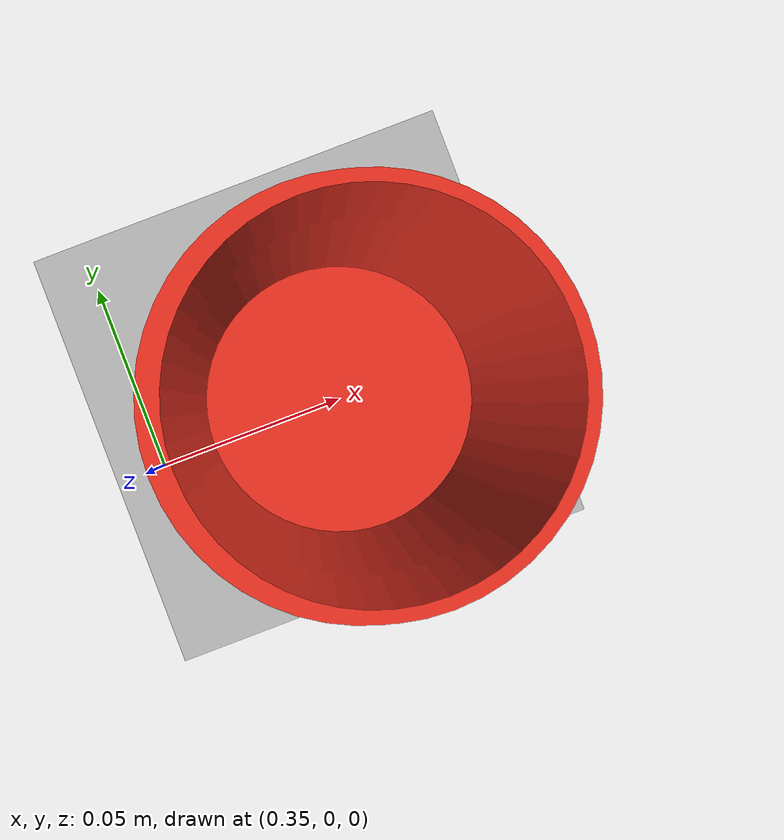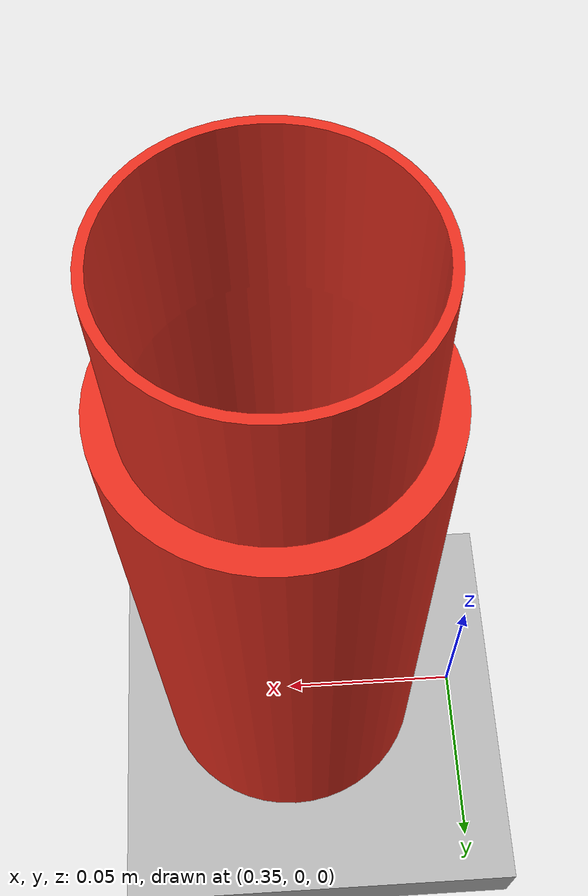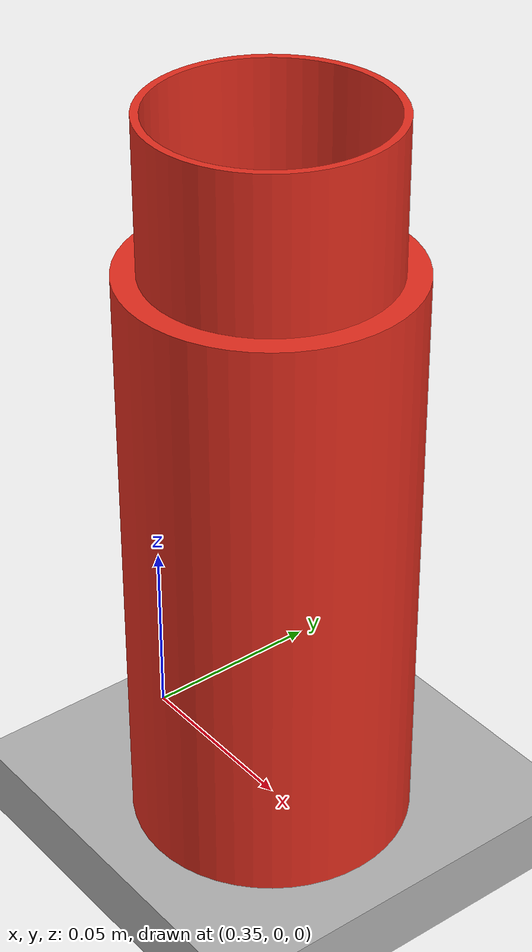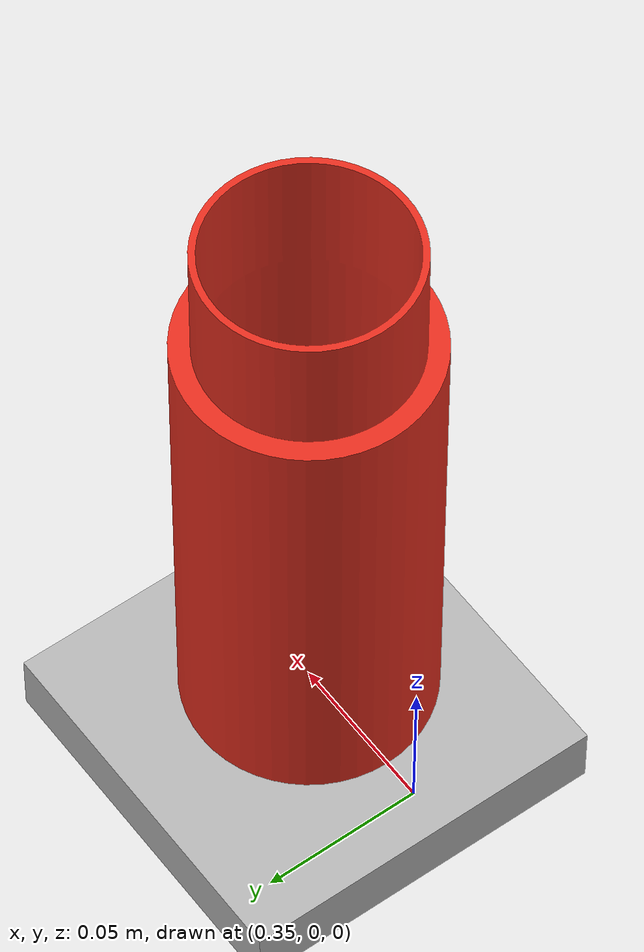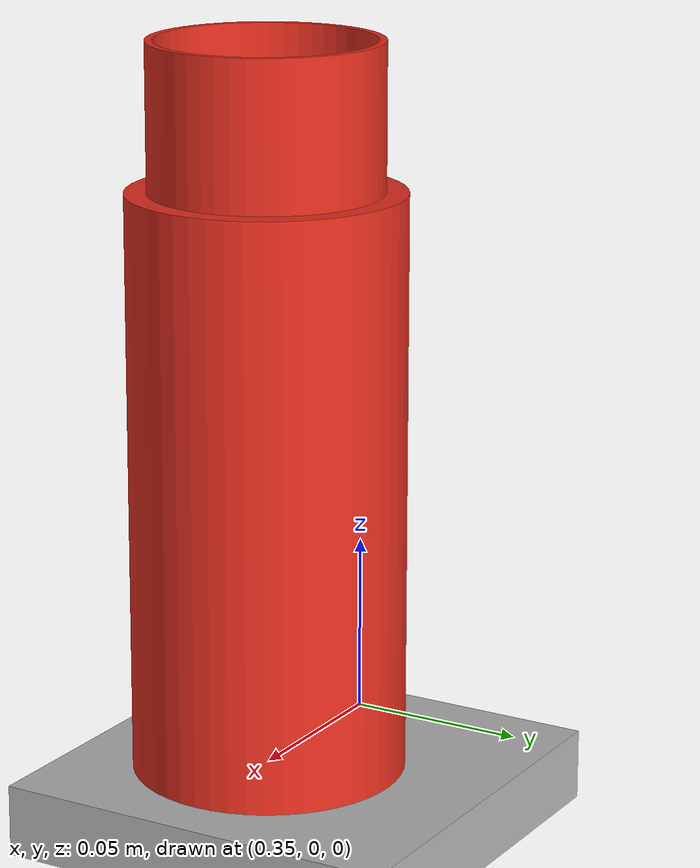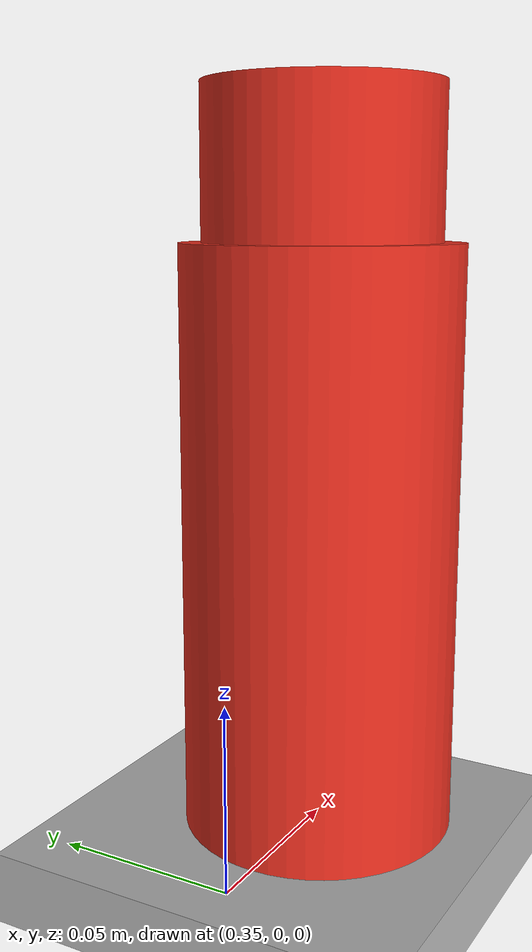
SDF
<?xml version='1.0' encoding='utf-8'?>
<sdf version="1.7">
  <world name="cup_geometry_probe">
    <gravity>0 0 -9.81</gravity>
    <physics type="ode">
      <max_step_size>.001</max_step_size>
      <real_time_update_rate>1000</real_time_update_rate>
    </physics>
    <light name="sun" type="directional">
      <pose>0 0 5 0 0 0</pose>
      <diffuse>.9 .9 .9 1</diffuse>
      <direction>-.4 .1 -1</direction>
    </light>
    <model name="probe_table">
      <static>true</static>
      <link name="top">
        <pose>.4 0 -.01 0 0 0</pose>
        <collision name="surface">
          <geometry>
            <box>
              <size>1 1 .02</size>
            </box>
          </geometry>
        </collision>
        <visual name="surface">
          <geometry>
            <box>
              <size>1 1 .02</size>
            </box>
          </geometry>
          <material>
            <ambient>.55 .55 .55 1</ambient>
            <diffuse>.7 .7 .7 1</diffuse>
          </material>
        </visual>
      </link>
    </model>
    <model name="stepped_cup">
      <static>false</static>
      <link name="cup_link">
        <gravity>true</gravity>
        <inertial>
          <pose>0 0 -0.00888728777286 0 0 0</pose>
          <mass>0.08</mass>
          <inertia>
            <ixx>0.00034252853401634735</ixx>
            <iyy>0.00034252853401634735</iyy>
            <izz>9.66588229419318e-05</izz>
            <ixy>0</ixy>
            <ixz>0</ixz>
            <iyz>0</iyz>
          </inertia>
        </inertial>
        <collision name="cup_shell_0">
          <geometry>
            <mesh>
              <uri>file:///home/young1x/robot_projects/piper_robot/simulation/validation/cup_vision/stepped_cup_probe/cup_model/section_00_000.stl</uri>
            </mesh>
          </geometry>
          <surface>
            <friction>
              <ode>
                <mu>1.2</mu>
                <mu2>1.2</mu2>
              </ode>
            </friction>
            <contact>
              <ode>
                <kp>100000</kp>
                <kd>10</kd>
                <max_vel>0.05</max_vel>
                <min_depth>0.0001</min_depth>
              </ode>
            </contact>
          </surface>
        </collision>
        <collision name="cup_shell_1">
          <geometry>
            <mesh>
              <uri>file:///home/young1x/robot_projects/piper_robot/simulation/validation/cup_vision/stepped_cup_probe/cup_model/section_00_001.stl</uri>
            </mesh>
          </geometry>
          <surface>
            <friction>
              <ode>
                <mu>1.2</mu>
                <mu2>1.2</mu2>
              </ode>
            </friction>
            <contact>
              <ode>
                <kp>100000</kp>
                <kd>10</kd>
                <max_vel>0.05</max_vel>
                <min_depth>0.0001</min_depth>
              </ode>
            </contact>
          </surface>
        </collision>
        <collision name="cup_shell_2">
          <geometry>
            <mesh>
              <uri>file:///home/young1x/robot_projects/piper_robot/simulation/validation/cup_vision/stepped_cup_probe/cup_model/section_00_002.stl</uri>
            </mesh>
          </geometry>
          <surface>
            <friction>
              <ode>
                <mu>1.2</mu>
                <mu2>1.2</mu2>
              </ode>
            </friction>
            <contact>
              <ode>
                <kp>100000</kp>
                <kd>10</kd>
                <max_vel>0.05</max_vel>
                <min_depth>0.0001</min_depth>
              </ode>
            </contact>
          </surface>
        </collision>
        <collision name="cup_shell_3">
          <geometry>
            <mesh>
              <uri>file:///home/young1x/robot_projects/piper_robot/simulation/validation/cup_vision/stepped_cup_probe/cup_model/section_00_003.stl</uri>
            </mesh>
          </geometry>
          <surface>
            <friction>
              <ode>
                <mu>1.2</mu>
                <mu2>1.2</mu2>
              </ode>
            </friction>
            <contact>
              <ode>
                <kp>100000</kp>
                <kd>10</kd>
                <max_vel>0.05</max_vel>
                <min_depth>0.0001</min_depth>
              </ode>
            </contact>
          </surface>
        </collision>
        <collision name="cup_shell_4">
          <geometry>
            <mesh>
              <uri>file:///home/young1x/robot_projects/piper_robot/simulation/validation/cup_vision/stepped_cup_probe/cup_model/section_00_004.stl</uri>
            </mesh>
          </geometry>
          <surface>
            <friction>
              <ode>
                <mu>1.2</mu>
                <mu2>1.2</mu2>
              </ode>
            </friction>
            <contact>
              <ode>
                <kp>100000</kp>
                <kd>10</kd>
                <max_vel>0.05</max_vel>
                <min_depth>0.0001</min_depth>
              </ode>
            </contact>
          </surface>
        </collision>
        <collision name="cup_shell_5">
          <geometry>
            <mesh>
              <uri>file:///home/young1x/robot_projects/piper_robot/simulation/validation/cup_vision/stepped_cup_probe/cup_model/section_00_005.stl</uri>
            </mesh>
          </geometry>
          <surface>
            <friction>
              <ode>
                <mu>1.2</mu>
                <mu2>1.2</mu2>
              </ode>
            </friction>
            <contact>
              <ode>
                <kp>100000</kp>
                <kd>10</kd>
                <max_vel>0.05</max_vel>
                <min_depth>0.0001</min_depth>
              </ode>
            </contact>
          </surface>
        </collision>
        <collision name="cup_shell_6">
          <geometry>
            <mesh>
              <uri>file:///home/young1x/robot_projects/piper_robot/simulation/validation/cup_vision/stepped_cup_probe/cup_model/section_00_006.stl</uri>
            </mesh>
          </geometry>
          <surface>
            <friction>
              <ode>
                <mu>1.2</mu>
                <mu2>1.2</mu2>
              </ode>
            </friction>
            <contact>
              <ode>
                <kp>100000</kp>
                <kd>10</kd>
                <max_vel>0.05</max_vel>
                <min_depth>0.0001</min_depth>
              </ode>
            </contact>
          </surface>
        </collision>
        <collision name="cup_shell_7">
          <geometry>
            <mesh>
              <uri>file:///home/young1x/robot_projects/piper_robot/simulation/validation/cup_vision/stepped_cup_probe/cup_model/section_00_007.stl</uri>
            </mesh>
          </geometry>
          <surface>
            <friction>
              <ode>
                <mu>1.2</mu>
                <mu2>1.2</mu2>
              </ode>
            </friction>
            <contact>
              <ode>
                <kp>100000</kp>
                <kd>10</kd>
                <max_vel>0.05</max_vel>
                <min_depth>0.0001</min_depth>
              </ode>
            </contact>
          </surface>
        </collision>
        <collision name="cup_shell_8">
          <geometry>
            <mesh>
              <uri>file:///home/young1x/robot_projects/piper_robot/simulation/validation/cup_vision/stepped_cup_probe/cup_model/section_00_008.stl</uri>
            </mesh>
          </geometry>
          <surface>
            <friction>
              <ode>
                <mu>1.2</mu>
                <mu2>1.2</mu2>
              </ode>
            </friction>
            <contact>
              <ode>
                <kp>100000</kp>
                <kd>10</kd>
                <max_vel>0.05</max_vel>
                <min_depth>0.0001</min_depth>
              </ode>
            </contact>
          </surface>
        </collision>
        <collision name="cup_shell_9">
          <geometry>
            <mesh>
              <uri>file:///home/young1x/robot_projects/piper_robot/simulation/validation/cup_vision/stepped_cup_probe/cup_model/section_00_009.stl</uri>
            </mesh>
          </geometry>
          <surface>
            <friction>
              <ode>
                <mu>1.2</mu>
                <mu2>1.2</mu2>
              </ode>
            </friction>
            <contact>
              <ode>
                <kp>100000</kp>
                <kd>10</kd>
                <max_vel>0.05</max_vel>
                <min_depth>0.0001</min_depth>
              </ode>
            </contact>
          </surface>
        </collision>
        <collision name="cup_shell_10">
          <geometry>
            <mesh>
              <uri>file:///home/young1x/robot_projects/piper_robot/simulation/validation/cup_vision/stepped_cup_probe/cup_model/section_00_010.stl</uri>
            </mesh>
          </geometry>
          <surface>
            <friction>
              <ode>
                <mu>1.2</mu>
                <mu2>1.2</mu2>
              </ode>
            </friction>
            <contact>
              <ode>
                <kp>100000</kp>
                <kd>10</kd>
                <max_vel>0.05</max_vel>
                <min_depth>0.0001</min_depth>
              </ode>
            </contact>
          </surface>
        </collision>
        <collision name="cup_shell_11">
          <geometry>
            <mesh>
              <uri>file:///home/young1x/robot_projects/piper_robot/simulation/validation/cup_vision/stepped_cup_probe/cup_model/section_00_011.stl</uri>
            </mesh>
          </geometry>
          <surface>
            <friction>
              <ode>
                <mu>1.2</mu>
                <mu2>1.2</mu2>
              </ode>
            </friction>
            <contact>
              <ode>
                <kp>100000</kp>
                <kd>10</kd>
                <max_vel>0.05</max_vel>
                <min_depth>0.0001</min_depth>
              </ode>
            </contact>
          </surface>
        </collision>
        <collision name="cup_shell_12">
          <geometry>
            <mesh>
              <uri>file:///home/young1x/robot_projects/piper_robot/simulation/validation/cup_vision/stepped_cup_probe/cup_model/section_00_012.stl</uri>
            </mesh>
          </geometry>
          <surface>
            <friction>
              <ode>
                <mu>1.2</mu>
                <mu2>1.2</mu2>
              </ode>
            </friction>
            <contact>
              <ode>
                <kp>100000</kp>
                <kd>10</kd>
                <max_vel>0.05</max_vel>
                <min_depth>0.0001</min_depth>
              </ode>
            </contact>
          </surface>
        </collision>
        <collision name="cup_shell_13">
          <geometry>
            <mesh>
              <uri>file:///home/young1x/robot_projects/piper_robot/simulation/validation/cup_vision/stepped_cup_probe/cup_model/section_00_013.stl</uri>
            </mesh>
          </geometry>
          <surface>
            <friction>
              <ode>
                <mu>1.2</mu>
                <mu2>1.2</mu2>
              </ode>
            </friction>
            <contact>
              <ode>
                <kp>100000</kp>
                <kd>10</kd>
                <max_vel>0.05</max_vel>
                <min_depth>0.0001</min_depth>
              </ode>
            </contact>
          </surface>
        </collision>
        <collision name="cup_shell_14">
          <geometry>
            <mesh>
              <uri>file:///home/young1x/robot_projects/piper_robot/simulation/validation/cup_vision/stepped_cup_probe/cup_model/section_00_014.stl</uri>
            </mesh>
          </geometry>
          <surface>
            <friction>
              <ode>
                <mu>1.2</mu>
                <mu2>1.2</mu2>
              </ode>
            </friction>
            <contact>
              <ode>
                <kp>100000</kp>
                <kd>10</kd>
                <max_vel>0.05</max_vel>
                <min_depth>0.0001</min_depth>
              </ode>
            </contact>
          </surface>
        </collision>
        <collision name="cup_shell_15">
          <geometry>
            <mesh>
              <uri>file:///home/young1x/robot_projects/piper_robot/simulation/validation/cup_vision/stepped_cup_probe/cup_model/section_00_015.stl</uri>
            </mesh>
          </geometry>
          <surface>
            <friction>
              <ode>
                <mu>1.2</mu>
                <mu2>1.2</mu2>
              </ode>
            </friction>
            <contact>
              <ode>
                <kp>100000</kp>
                <kd>10</kd>
                <max_vel>0.05</max_vel>
                <min_depth>0.0001</min_depth>
              </ode>
            </contact>
          </surface>
        </collision>
        <collision name="cup_shell_16">
          <geometry>
            <mesh>
              <uri>file:///home/young1x/robot_projects/piper_robot/simulation/validation/cup_vision/stepped_cup_probe/cup_model/section_00_016.stl</uri>
            </mesh>
          </geometry>
          <surface>
            <friction>
              <ode>
                <mu>1.2</mu>
                <mu2>1.2</mu2>
              </ode>
            </friction>
            <contact>
              <ode>
                <kp>100000</kp>
                <kd>10</kd>
                <max_vel>0.05</max_vel>
                <min_depth>0.0001</min_depth>
              </ode>
            </contact>
          </surface>
        </collision>
        <collision name="cup_shell_17">
          <geometry>
            <mesh>
              <uri>file:///home/young1x/robot_projects/piper_robot/simulation/validation/cup_vision/stepped_cup_probe/cup_model/section_00_017.stl</uri>
            </mesh>
          </geometry>
          <surface>
            <friction>
              <ode>
                <mu>1.2</mu>
                <mu2>1.2</mu2>
              </ode>
            </friction>
            <contact>
              <ode>
                <kp>100000</kp>
                <kd>10</kd>
                <max_vel>0.05</max_vel>
                <min_depth>0.0001</min_depth>
              </ode>
            </contact>
          </surface>
        </collision>
        <collision name="cup_shell_18">
          <geometry>
            <mesh>
              <uri>file:///home/young1x/robot_projects/piper_robot/simulation/validation/cup_vision/stepped_cup_probe/cup_model/section_00_018.stl</uri>
            </mesh>
          </geometry>
          <surface>
            <friction>
              <ode>
                <mu>1.2</mu>
                <mu2>1.2</mu2>
              </ode>
            </friction>
            <contact>
              <ode>
                <kp>100000</kp>
                <kd>10</kd>
                <max_vel>0.05</max_vel>
                <min_depth>0.0001</min_depth>
              </ode>
            </contact>
          </surface>
        </collision>
        <collision name="cup_shell_19">
          <geometry>
            <mesh>
              <uri>file:///home/young1x/robot_projects/piper_robot/simulation/validation/cup_vision/stepped_cup_probe/cup_model/section_00_019.stl</uri>
            </mesh>
          </geometry>
          <surface>
            <friction>
              <ode>
                <mu>1.2</mu>
                <mu2>1.2</mu2>
              </ode>
            </friction>
            <contact>
              <ode>
                <kp>100000</kp>
                <kd>10</kd>
                <max_vel>0.05</max_vel>
                <min_depth>0.0001</min_depth>
              </ode>
            </contact>
          </surface>
        </collision>
        <collision name="cup_shell_20">
          <geometry>
            <mesh>
              <uri>file:///home/young1x/robot_projects/piper_robot/simulation/validation/cup_vision/stepped_cup_probe/cup_model/section_00_020.stl</uri>
            </mesh>
          </geometry>
          <surface>
            <friction>
              <ode>
                <mu>1.2</mu>
                <mu2>1.2</mu2>
              </ode>
            </friction>
            <contact>
              <ode>
                <kp>100000</kp>
                <kd>10</kd>
                <max_vel>0.05</max_vel>
                <min_depth>0.0001</min_depth>
              </ode>
            </contact>
          </surface>
        </collision>
        <collision name="cup_shell_21">
          <geometry>
            <mesh>
              <uri>file:///home/young1x/robot_projects/piper_robot/simulation/validation/cup_vision/stepped_cup_probe/cup_model/section_00_021.stl</uri>
            </mesh>
          </geometry>
          <surface>
            <friction>
              <ode>
                <mu>1.2</mu>
                <mu2>1.2</mu2>
              </ode>
            </friction>
            <contact>
              <ode>
                <kp>100000</kp>
                <kd>10</kd>
                <max_vel>0.05</max_vel>
                <min_depth>0.0001</min_depth>
              </ode>
            </contact>
          </surface>
        </collision>
        <collision name="cup_shell_22">
          <geometry>
            <mesh>
              <uri>file:///home/young1x/robot_projects/piper_robot/simulation/validation/cup_vision/stepped_cup_probe/cup_model/section_00_022.stl</uri>
            </mesh>
          </geometry>
          <surface>
            <friction>
              <ode>
                <mu>1.2</mu>
                <mu2>1.2</mu2>
              </ode>
            </friction>
            <contact>
              <ode>
                <kp>100000</kp>
                <kd>10</kd>
                <max_vel>0.05</max_vel>
                <min_depth>0.0001</min_depth>
              </ode>
            </contact>
          </surface>
        </collision>
        <collision name="cup_shell_23">
          <geometry>
            <mesh>
              <uri>file:///home/young1x/robot_projects/piper_robot/simulation/validation/cup_vision/stepped_cup_probe/cup_model/section_00_023.stl</uri>
            </mesh>
          </geometry>
          <surface>
            <friction>
              <ode>
                <mu>1.2</mu>
                <mu2>1.2</mu2>
              </ode>
            </friction>
            <contact>
              <ode>
                <kp>100000</kp>
                <kd>10</kd>
                <max_vel>0.05</max_vel>
                <min_depth>0.0001</min_depth>
              </ode>
            </contact>
          </surface>
        </collision>
        <collision name="cup_shell_24">
          <geometry>
            <mesh>
              <uri>file:///home/young1x/robot_projects/piper_robot/simulation/validation/cup_vision/stepped_cup_probe/cup_model/section_00_024.stl</uri>
            </mesh>
          </geometry>
          <surface>
            <friction>
              <ode>
                <mu>1.2</mu>
                <mu2>1.2</mu2>
              </ode>
            </friction>
            <contact>
              <ode>
                <kp>100000</kp>
                <kd>10</kd>
                <max_vel>0.05</max_vel>
                <min_depth>0.0001</min_depth>
              </ode>
            </contact>
          </surface>
        </collision>
        <collision name="cup_shell_25">
          <geometry>
            <mesh>
              <uri>file:///home/young1x/robot_projects/piper_robot/simulation/validation/cup_vision/stepped_cup_probe/cup_model/section_00_025.stl</uri>
            </mesh>
          </geometry>
          <surface>
            <friction>
              <ode>
                <mu>1.2</mu>
                <mu2>1.2</mu2>
              </ode>
            </friction>
            <contact>
              <ode>
                <kp>100000</kp>
                <kd>10</kd>
                <max_vel>0.05</max_vel>
                <min_depth>0.0001</min_depth>
              </ode>
            </contact>
          </surface>
        </collision>
        <collision name="cup_shell_26">
          <geometry>
            <mesh>
              <uri>file:///home/young1x/robot_projects/piper_robot/simulation/validation/cup_vision/stepped_cup_probe/cup_model/section_00_026.stl</uri>
            </mesh>
          </geometry>
          <surface>
            <friction>
              <ode>
                <mu>1.2</mu>
                <mu2>1.2</mu2>
              </ode>
            </friction>
            <contact>
              <ode>
                <kp>100000</kp>
                <kd>10</kd>
                <max_vel>0.05</max_vel>
                <min_depth>0.0001</min_depth>
              </ode>
            </contact>
          </surface>
        </collision>
        <collision name="cup_shell_27">
          <geometry>
            <mesh>
              <uri>file:///home/young1x/robot_projects/piper_robot/simulation/validation/cup_vision/stepped_cup_probe/cup_model/section_00_027.stl</uri>
            </mesh>
          </geometry>
          <surface>
            <friction>
              <ode>
                <mu>1.2</mu>
                <mu2>1.2</mu2>
              </ode>
            </friction>
            <contact>
              <ode>
                <kp>100000</kp>
                <kd>10</kd>
                <max_vel>0.05</max_vel>
                <min_depth>0.0001</min_depth>
              </ode>
            </contact>
          </surface>
        </collision>
        <collision name="cup_shell_28">
          <geometry>
            <mesh>
              <uri>file:///home/young1x/robot_projects/piper_robot/simulation/validation/cup_vision/stepped_cup_probe/cup_model/section_00_028.stl</uri>
            </mesh>
          </geometry>
          <surface>
            <friction>
              <ode>
                <mu>1.2</mu>
                <mu2>1.2</mu2>
              </ode>
            </friction>
            <contact>
              <ode>
                <kp>100000</kp>
                <kd>10</kd>
                <max_vel>0.05</max_vel>
                <min_depth>0.0001</min_depth>
              </ode>
            </contact>
          </surface>
        </collision>
        <collision name="cup_shell_29">
          <geometry>
            <mesh>
              <uri>file:///home/young1x/robot_projects/piper_robot/simulation/validation/cup_vision/stepped_cup_probe/cup_model/section_00_029.stl</uri>
            </mesh>
          </geometry>
          <surface>
            <friction>
              <ode>
                <mu>1.2</mu>
                <mu2>1.2</mu2>
              </ode>
            </friction>
            <contact>
              <ode>
                <kp>100000</kp>
                <kd>10</kd>
                <max_vel>0.05</max_vel>
                <min_depth>0.0001</min_depth>
              </ode>
            </contact>
          </surface>
        </collision>
        <collision name="cup_shell_30">
          <geometry>
            <mesh>
              <uri>file:///home/young1x/robot_projects/piper_robot/simulation/validation/cup_vision/stepped_cup_probe/cup_model/section_00_030.stl</uri>
            </mesh>
          </geometry>
          <surface>
            <friction>
              <ode>
                <mu>1.2</mu>
                <mu2>1.2</mu2>
              </ode>
            </friction>
            <contact>
              <ode>
                <kp>100000</kp>
                <kd>10</kd>
                <max_vel>0.05</max_vel>
                <min_depth>0.0001</min_depth>
              </ode>
            </contact>
          </surface>
        </collision>
        <collision name="cup_shell_31">
          <geometry>
            <mesh>
              <uri>file:///home/young1x/robot_projects/piper_robot/simulation/validation/cup_vision/stepped_cup_probe/cup_model/section_00_031.stl</uri>
            </mesh>
          </geometry>
          <surface>
            <friction>
              <ode>
                <mu>1.2</mu>
                <mu2>1.2</mu2>
              </ode>
            </friction>
            <contact>
              <ode>
                <kp>100000</kp>
                <kd>10</kd>
                <max_vel>0.05</max_vel>
                <min_depth>0.0001</min_depth>
              </ode>
            </contact>
          </surface>
        </collision>
        <collision name="cup_shell_32">
          <geometry>
            <mesh>
              <uri>file:///home/young1x/robot_projects/piper_robot/simulation/validation/cup_vision/stepped_cup_probe/cup_model/section_00_032.stl</uri>
            </mesh>
          </geometry>
          <surface>
            <friction>
              <ode>
                <mu>1.2</mu>
                <mu2>1.2</mu2>
              </ode>
            </friction>
            <contact>
              <ode>
                <kp>100000</kp>
                <kd>10</kd>
                <max_vel>0.05</max_vel>
                <min_depth>0.0001</min_depth>
              </ode>
            </contact>
          </surface>
        </collision>
        <collision name="cup_shell_33">
          <geometry>
            <mesh>
              <uri>file:///home/young1x/robot_projects/piper_robot/simulation/validation/cup_vision/stepped_cup_probe/cup_model/section_00_033.stl</uri>
            </mesh>
          </geometry>
          <surface>
            <friction>
              <ode>
                <mu>1.2</mu>
                <mu2>1.2</mu2>
              </ode>
            </friction>
            <contact>
              <ode>
                <kp>100000</kp>
                <kd>10</kd>
                <max_vel>0.05</max_vel>
                <min_depth>0.0001</min_depth>
              </ode>
            </contact>
          </surface>
        </collision>
        <collision name="cup_shell_34">
          <geometry>
            <mesh>
              <uri>file:///home/young1x/robot_projects/piper_robot/simulation/validation/cup_vision/stepped_cup_probe/cup_model/section_00_034.stl</uri>
            </mesh>
          </geometry>
          <surface>
            <friction>
              <ode>
                <mu>1.2</mu>
                <mu2>1.2</mu2>
              </ode>
            </friction>
            <contact>
              <ode>
                <kp>100000</kp>
                <kd>10</kd>
                <max_vel>0.05</max_vel>
                <min_depth>0.0001</min_depth>
              </ode>
            </contact>
          </surface>
        </collision>
        <collision name="cup_shell_35">
          <geometry>
            <mesh>
              <uri>file:///home/young1x/robot_projects/piper_robot/simulation/validation/cup_vision/stepped_cup_probe/cup_model/section_00_035.stl</uri>
            </mesh>
          </geometry>
          <surface>
            <friction>
              <ode>
                <mu>1.2</mu>
                <mu2>1.2</mu2>
              </ode>
            </friction>
            <contact>
              <ode>
                <kp>100000</kp>
                <kd>10</kd>
                <max_vel>0.05</max_vel>
                <min_depth>0.0001</min_depth>
              </ode>
            </contact>
          </surface>
        </collision>
        <collision name="cup_shell_36">
          <geometry>
            <mesh>
              <uri>file:///home/young1x/robot_projects/piper_robot/simulation/validation/cup_vision/stepped_cup_probe/cup_model/section_00_036.stl</uri>
            </mesh>
          </geometry>
          <surface>
            <friction>
              <ode>
                <mu>1.2</mu>
                <mu2>1.2</mu2>
              </ode>
            </friction>
            <contact>
              <ode>
                <kp>100000</kp>
                <kd>10</kd>
                <max_vel>0.05</max_vel>
                <min_depth>0.0001</min_depth>
              </ode>
            </contact>
          </surface>
        </collision>
        <collision name="cup_shell_37">
          <geometry>
            <mesh>
              <uri>file:///home/young1x/robot_projects/piper_robot/simulation/validation/cup_vision/stepped_cup_probe/cup_model/section_00_037.stl</uri>
            </mesh>
          </geometry>
          <surface>
            <friction>
              <ode>
                <mu>1.2</mu>
                <mu2>1.2</mu2>
              </ode>
            </friction>
            <contact>
              <ode>
                <kp>100000</kp>
                <kd>10</kd>
                <max_vel>0.05</max_vel>
                <min_depth>0.0001</min_depth>
              </ode>
            </contact>
          </surface>
        </collision>
        <collision name="cup_shell_38">
          <geometry>
            <mesh>
              <uri>file:///home/young1x/robot_projects/piper_robot/simulation/validation/cup_vision/stepped_cup_probe/cup_model/section_00_038.stl</uri>
            </mesh>
          </geometry>
          <surface>
            <friction>
              <ode>
                <mu>1.2</mu>
                <mu2>1.2</mu2>
              </ode>
            </friction>
            <contact>
              <ode>
                <kp>100000</kp>
                <kd>10</kd>
                <max_vel>0.05</max_vel>
                <min_depth>0.0001</min_depth>
              </ode>
            </contact>
          </surface>
        </collision>
        <collision name="cup_shell_39">
          <geometry>
            <mesh>
              <uri>file:///home/young1x/robot_projects/piper_robot/simulation/validation/cup_vision/stepped_cup_probe/cup_model/section_00_039.stl</uri>
            </mesh>
          </geometry>
          <surface>
            <friction>
              <ode>
                <mu>1.2</mu>
                <mu2>1.2</mu2>
              </ode>
            </friction>
            <contact>
              <ode>
                <kp>100000</kp>
                <kd>10</kd>
                <max_vel>0.05</max_vel>
                <min_depth>0.0001</min_depth>
              </ode>
            </contact>
          </surface>
        </collision>
        <collision name="cup_shell_40">
          <geometry>
            <mesh>
              <uri>file:///home/young1x/robot_projects/piper_robot/simulation/validation/cup_vision/stepped_cup_probe/cup_model/section_00_040.stl</uri>
            </mesh>
          </geometry>
          <surface>
            <friction>
              <ode>
                <mu>1.2</mu>
                <mu2>1.2</mu2>
              </ode>
            </friction>
            <contact>
              <ode>
                <kp>100000</kp>
                <kd>10</kd>
                <max_vel>0.05</max_vel>
                <min_depth>0.0001</min_depth>
              </ode>
            </contact>
          </surface>
        </collision>
        <collision name="cup_shell_41">
          <geometry>
            <mesh>
              <uri>file:///home/young1x/robot_projects/piper_robot/simulation/validation/cup_vision/stepped_cup_probe/cup_model/section_00_041.stl</uri>
            </mesh>
          </geometry>
          <surface>
            <friction>
              <ode>
                <mu>1.2</mu>
                <mu2>1.2</mu2>
              </ode>
            </friction>
            <contact>
              <ode>
                <kp>100000</kp>
                <kd>10</kd>
                <max_vel>0.05</max_vel>
                <min_depth>0.0001</min_depth>
              </ode>
            </contact>
          </surface>
        </collision>
        <collision name="cup_shell_42">
          <geometry>
            <mesh>
              <uri>file:///home/young1x/robot_projects/piper_robot/simulation/validation/cup_vision/stepped_cup_probe/cup_model/section_00_042.stl</uri>
            </mesh>
          </geometry>
          <surface>
            <friction>
              <ode>
                <mu>1.2</mu>
                <mu2>1.2</mu2>
              </ode>
            </friction>
            <contact>
              <ode>
                <kp>100000</kp>
                <kd>10</kd>
                <max_vel>0.05</max_vel>
                <min_depth>0.0001</min_depth>
              </ode>
            </contact>
          </surface>
        </collision>
        <collision name="cup_shell_43">
          <geometry>
            <mesh>
              <uri>file:///home/young1x/robot_projects/piper_robot/simulation/validation/cup_vision/stepped_cup_probe/cup_model/section_00_043.stl</uri>
            </mesh>
          </geometry>
          <surface>
            <friction>
              <ode>
                <mu>1.2</mu>
                <mu2>1.2</mu2>
              </ode>
            </friction>
            <contact>
              <ode>
                <kp>100000</kp>
                <kd>10</kd>
                <max_vel>0.05</max_vel>
                <min_depth>0.0001</min_depth>
              </ode>
            </contact>
          </surface>
        </collision>
        <collision name="cup_shell_44">
          <geometry>
            <mesh>
              <uri>file:///home/young1x/robot_projects/piper_robot/simulation/validation/cup_vision/stepped_cup_probe/cup_model/section_00_044.stl</uri>
            </mesh>
          </geometry>
          <surface>
            <friction>
              <ode>
                <mu>1.2</mu>
                <mu2>1.2</mu2>
              </ode>
            </friction>
            <contact>
              <ode>
                <kp>100000</kp>
                <kd>10</kd>
                <max_vel>0.05</max_vel>
                <min_depth>0.0001</min_depth>
              </ode>
            </contact>
          </surface>
        </collision>
        <collision name="cup_shell_45">
          <geometry>
            <mesh>
              <uri>file:///home/young1x/robot_projects/piper_robot/simulation/validation/cup_vision/stepped_cup_probe/cup_model/section_00_045.stl</uri>
            </mesh>
          </geometry>
          <surface>
            <friction>
              <ode>
                <mu>1.2</mu>
                <mu2>1.2</mu2>
              </ode>
            </friction>
            <contact>
              <ode>
                <kp>100000</kp>
                <kd>10</kd>
                <max_vel>0.05</max_vel>
                <min_depth>0.0001</min_depth>
              </ode>
            </contact>
          </surface>
        </collision>
        <collision name="cup_shell_46">
          <geometry>
            <mesh>
              <uri>file:///home/young1x/robot_projects/piper_robot/simulation/validation/cup_vision/stepped_cup_probe/cup_model/section_00_046.stl</uri>
            </mesh>
          </geometry>
          <surface>
            <friction>
              <ode>
                <mu>1.2</mu>
                <mu2>1.2</mu2>
              </ode>
            </friction>
            <contact>
              <ode>
                <kp>100000</kp>
                <kd>10</kd>
                <max_vel>0.05</max_vel>
                <min_depth>0.0001</min_depth>
              </ode>
            </contact>
          </surface>
        </collision>
        <collision name="cup_shell_47">
          <geometry>
            <mesh>
              <uri>file:///home/young1x/robot_projects/piper_robot/simulation/validation/cup_vision/stepped_cup_probe/cup_model/section_00_047.stl</uri>
            </mesh>
          </geometry>
          <surface>
            <friction>
              <ode>
                <mu>1.2</mu>
                <mu2>1.2</mu2>
              </ode>
            </friction>
            <contact>
              <ode>
                <kp>100000</kp>
                <kd>10</kd>
                <max_vel>0.05</max_vel>
                <min_depth>0.0001</min_depth>
              </ode>
            </contact>
          </surface>
        </collision>
        <collision name="cup_shell_48">
          <geometry>
            <mesh>
              <uri>file:///home/young1x/robot_projects/piper_robot/simulation/validation/cup_vision/stepped_cup_probe/cup_model/section_01_000.stl</uri>
            </mesh>
          </geometry>
          <surface>
            <friction>
              <ode>
                <mu>1.2</mu>
                <mu2>1.2</mu2>
              </ode>
            </friction>
            <contact>
              <ode>
                <kp>100000</kp>
                <kd>10</kd>
                <max_vel>0.05</max_vel>
                <min_depth>0.0001</min_depth>
              </ode>
            </contact>
          </surface>
        </collision>
        <collision name="cup_shell_49">
          <geometry>
            <mesh>
              <uri>file:///home/young1x/robot_projects/piper_robot/simulation/validation/cup_vision/stepped_cup_probe/cup_model/section_01_001.stl</uri>
            </mesh>
          </geometry>
          <surface>
            <friction>
              <ode>
                <mu>1.2</mu>
                <mu2>1.2</mu2>
              </ode>
            </friction>
            <contact>
              <ode>
                <kp>100000</kp>
                <kd>10</kd>
                <max_vel>0.05</max_vel>
                <min_depth>0.0001</min_depth>
              </ode>
            </contact>
          </surface>
        </collision>
        <collision name="cup_shell_50">
          <geometry>
            <mesh>
              <uri>file:///home/young1x/robot_projects/piper_robot/simulation/validation/cup_vision/stepped_cup_probe/cup_model/section_01_002.stl</uri>
            </mesh>
          </geometry>
          <surface>
            <friction>
              <ode>
                <mu>1.2</mu>
                <mu2>1.2</mu2>
              </ode>
            </friction>
            <contact>
              <ode>
                <kp>100000</kp>
                <kd>10</kd>
                <max_vel>0.05</max_vel>
                <min_depth>0.0001</min_depth>
              </ode>
            </contact>
          </surface>
        </collision>
        <collision name="cup_shell_51">
          <geometry>
            <mesh>
              <uri>file:///home/young1x/robot_projects/piper_robot/simulation/validation/cup_vision/stepped_cup_probe/cup_model/section_01_003.stl</uri>
            </mesh>
          </geometry>
          <surface>
            <friction>
              <ode>
                <mu>1.2</mu>
                <mu2>1.2</mu2>
              </ode>
            </friction>
            <contact>
              <ode>
                <kp>100000</kp>
                <kd>10</kd>
                <max_vel>0.05</max_vel>
                <min_depth>0.0001</min_depth>
              </ode>
            </contact>
          </surface>
        </collision>
        <collision name="cup_shell_52">
          <geometry>
            <mesh>
              <uri>file:///home/young1x/robot_projects/piper_robot/simulation/validation/cup_vision/stepped_cup_probe/cup_model/section_01_004.stl</uri>
            </mesh>
          </geometry>
          <surface>
            <friction>
              <ode>
                <mu>1.2</mu>
                <mu2>1.2</mu2>
              </ode>
            </friction>
            <contact>
              <ode>
                <kp>100000</kp>
                <kd>10</kd>
                <max_vel>0.05</max_vel>
                <min_depth>0.0001</min_depth>
              </ode>
            </contact>
          </surface>
        </collision>
        <collision name="cup_shell_53">
          <geometry>
            <mesh>
              <uri>file:///home/young1x/robot_projects/piper_robot/simulation/validation/cup_vision/stepped_cup_probe/cup_model/section_01_005.stl</uri>
            </mesh>
          </geometry>
          <surface>
            <friction>
              <ode>
                <mu>1.2</mu>
                <mu2>1.2</mu2>
              </ode>
            </friction>
            <contact>
              <ode>
                <kp>100000</kp>
                <kd>10</kd>
                <max_vel>0.05</max_vel>
                <min_depth>0.0001</min_depth>
              </ode>
            </contact>
          </surface>
        </collision>
        <collision name="cup_shell_54">
          <geometry>
            <mesh>
              <uri>file:///home/young1x/robot_projects/piper_robot/simulation/validation/cup_vision/stepped_cup_probe/cup_model/section_01_006.stl</uri>
            </mesh>
          </geometry>
          <surface>
            <friction>
              <ode>
                <mu>1.2</mu>
                <mu2>1.2</mu2>
              </ode>
            </friction>
            <contact>
              <ode>
                <kp>100000</kp>
                <kd>10</kd>
                <max_vel>0.05</max_vel>
                <min_depth>0.0001</min_depth>
              </ode>
            </contact>
          </surface>
        </collision>
        <collision name="cup_shell_55">
          <geometry>
            <mesh>
              <uri>file:///home/young1x/robot_projects/piper_robot/simulation/validation/cup_vision/stepped_cup_probe/cup_model/section_01_007.stl</uri>
            </mesh>
          </geometry>
          <surface>
            <friction>
              <ode>
                <mu>1.2</mu>
                <mu2>1.2</mu2>
              </ode>
            </friction>
            <contact>
              <ode>
                <kp>100000</kp>
                <kd>10</kd>
                <max_vel>0.05</max_vel>
                <min_depth>0.0001</min_depth>
              </ode>
            </contact>
          </surface>
        </collision>
        <collision name="cup_shell_56">
          <geometry>
            <mesh>
              <uri>file:///home/young1x/robot_projects/piper_robot/simulation/validation/cup_vision/stepped_cup_probe/cup_model/section_01_008.stl</uri>
            </mesh>
          </geometry>
          <surface>
            <friction>
              <ode>
                <mu>1.2</mu>
                <mu2>1.2</mu2>
              </ode>
            </friction>
            <contact>
              <ode>
                <kp>100000</kp>
                <kd>10</kd>
                <max_vel>0.05</max_vel>
                <min_depth>0.0001</min_depth>
              </ode>
            </contact>
          </surface>
        </collision>
        <collision name="cup_shell_57">
          <geometry>
            <mesh>
              <uri>file:///home/young1x/robot_projects/piper_robot/simulation/validation/cup_vision/stepped_cup_probe/cup_model/section_01_009.stl</uri>
            </mesh>
          </geometry>
          <surface>
            <friction>
              <ode>
                <mu>1.2</mu>
                <mu2>1.2</mu2>
              </ode>
            </friction>
            <contact>
              <ode>
                <kp>100000</kp>
                <kd>10</kd>
                <max_vel>0.05</max_vel>
                <min_depth>0.0001</min_depth>
              </ode>
            </contact>
          </surface>
        </collision>
        <collision name="cup_shell_58">
          <geometry>
            <mesh>
              <uri>file:///home/young1x/robot_projects/piper_robot/simulation/validation/cup_vision/stepped_cup_probe/cup_model/section_01_010.stl</uri>
            </mesh>
          </geometry>
          <surface>
            <friction>
              <ode>
                <mu>1.2</mu>
                <mu2>1.2</mu2>
              </ode>
            </friction>
            <contact>
              <ode>
                <kp>100000</kp>
                <kd>10</kd>
                <max_vel>0.05</max_vel>
                <min_depth>0.0001</min_depth>
              </ode>
            </contact>
          </surface>
        </collision>
        <collision name="cup_shell_59">
          <geometry>
            <mesh>
              <uri>file:///home/young1x/robot_projects/piper_robot/simulation/validation/cup_vision/stepped_cup_probe/cup_model/section_01_011.stl</uri>
            </mesh>
          </geometry>
          <surface>
            <friction>
              <ode>
                <mu>1.2</mu>
                <mu2>1.2</mu2>
              </ode>
            </friction>
            <contact>
              <ode>
                <kp>100000</kp>
                <kd>10</kd>
                <max_vel>0.05</max_vel>
                <min_depth>0.0001</min_depth>
              </ode>
            </contact>
          </surface>
        </collision>
        <collision name="cup_shell_60">
          <geometry>
            <mesh>
              <uri>file:///home/young1x/robot_projects/piper_robot/simulation/validation/cup_vision/stepped_cup_probe/cup_model/section_01_012.stl</uri>
            </mesh>
          </geometry>
          <surface>
            <friction>
              <ode>
                <mu>1.2</mu>
                <mu2>1.2</mu2>
              </ode>
            </friction>
            <contact>
              <ode>
                <kp>100000</kp>
                <kd>10</kd>
                <max_vel>0.05</max_vel>
                <min_depth>0.0001</min_depth>
              </ode>
            </contact>
          </surface>
        </collision>
        <collision name="cup_shell_61">
          <geometry>
            <mesh>
              <uri>file:///home/young1x/robot_projects/piper_robot/simulation/validation/cup_vision/stepped_cup_probe/cup_model/section_01_013.stl</uri>
            </mesh>
          </geometry>
          <surface>
            <friction>
              <ode>
                <mu>1.2</mu>
                <mu2>1.2</mu2>
              </ode>
            </friction>
            <contact>
              <ode>
                <kp>100000</kp>
                <kd>10</kd>
                <max_vel>0.05</max_vel>
                <min_depth>0.0001</min_depth>
              </ode>
            </contact>
          </surface>
        </collision>
        <collision name="cup_shell_62">
          <geometry>
            <mesh>
              <uri>file:///home/young1x/robot_projects/piper_robot/simulation/validation/cup_vision/stepped_cup_probe/cup_model/section_01_014.stl</uri>
            </mesh>
          </geometry>
          <surface>
            <friction>
              <ode>
                <mu>1.2</mu>
                <mu2>1.2</mu2>
              </ode>
            </friction>
            <contact>
              <ode>
                <kp>100000</kp>
                <kd>10</kd>
                <max_vel>0.05</max_vel>
                <min_depth>0.0001</min_depth>
              </ode>
            </contact>
          </surface>
        </collision>
        <collision name="cup_shell_63">
          <geometry>
            <mesh>
              <uri>file:///home/young1x/robot_projects/piper_robot/simulation/validation/cup_vision/stepped_cup_probe/cup_model/section_01_015.stl</uri>
            </mesh>
          </geometry>
          <surface>
            <friction>
              <ode>
                <mu>1.2</mu>
                <mu2>1.2</mu2>
              </ode>
            </friction>
            <contact>
              <ode>
                <kp>100000</kp>
                <kd>10</kd>
                <max_vel>0.05</max_vel>
                <min_depth>0.0001</min_depth>
              </ode>
            </contact>
          </surface>
        </collision>
        <collision name="cup_shell_64">
          <geometry>
            <mesh>
              <uri>file:///home/young1x/robot_projects/piper_robot/simulation/validation/cup_vision/stepped_cup_probe/cup_model/section_01_016.stl</uri>
            </mesh>
          </geometry>
          <surface>
            <friction>
              <ode>
                <mu>1.2</mu>
                <mu2>1.2</mu2>
              </ode>
            </friction>
            <contact>
              <ode>
                <kp>100000</kp>
                <kd>10</kd>
                <max_vel>0.05</max_vel>
                <min_depth>0.0001</min_depth>
              </ode>
            </contact>
          </surface>
        </collision>
        <collision name="cup_shell_65">
          <geometry>
            <mesh>
              <uri>file:///home/young1x/robot_projects/piper_robot/simulation/validation/cup_vision/stepped_cup_probe/cup_model/section_01_017.stl</uri>
            </mesh>
          </geometry>
          <surface>
            <friction>
              <ode>
                <mu>1.2</mu>
                <mu2>1.2</mu2>
              </ode>
            </friction>
            <contact>
              <ode>
                <kp>100000</kp>
                <kd>10</kd>
                <max_vel>0.05</max_vel>
                <min_depth>0.0001</min_depth>
              </ode>
            </contact>
          </surface>
        </collision>
        <collision name="cup_shell_66">
          <geometry>
            <mesh>
              <uri>file:///home/young1x/robot_projects/piper_robot/simulation/validation/cup_vision/stepped_cup_probe/cup_model/section_01_018.stl</uri>
            </mesh>
          </geometry>
          <surface>
            <friction>
              <ode>
                <mu>1.2</mu>
                <mu2>1.2</mu2>
              </ode>
            </friction>
            <contact>
              <ode>
                <kp>100000</kp>
                <kd>10</kd>
                <max_vel>0.05</max_vel>
                <min_depth>0.0001</min_depth>
              </ode>
            </contact>
          </surface>
        </collision>
        <collision name="cup_shell_67">
          <geometry>
            <mesh>
              <uri>file:///home/young1x/robot_projects/piper_robot/simulation/validation/cup_vision/stepped_cup_probe/cup_model/section_01_019.stl</uri>
            </mesh>
          </geometry>
          <surface>
            <friction>
              <ode>
                <mu>1.2</mu>
                <mu2>1.2</mu2>
              </ode>
            </friction>
            <contact>
              <ode>
                <kp>100000</kp>
                <kd>10</kd>
                <max_vel>0.05</max_vel>
                <min_depth>0.0001</min_depth>
              </ode>
            </contact>
          </surface>
        </collision>
        <collision name="cup_shell_68">
          <geometry>
            <mesh>
              <uri>file:///home/young1x/robot_projects/piper_robot/simulation/validation/cup_vision/stepped_cup_probe/cup_model/section_01_020.stl</uri>
            </mesh>
          </geometry>
          <surface>
            <friction>
              <ode>
                <mu>1.2</mu>
                <mu2>1.2</mu2>
              </ode>
            </friction>
            <contact>
              <ode>
                <kp>100000</kp>
                <kd>10</kd>
                <max_vel>0.05</max_vel>
                <min_depth>0.0001</min_depth>
              </ode>
            </contact>
          </surface>
        </collision>
        <collision name="cup_shell_69">
          <geometry>
            <mesh>
              <uri>file:///home/young1x/robot_projects/piper_robot/simulation/validation/cup_vision/stepped_cup_probe/cup_model/section_01_021.stl</uri>
            </mesh>
          </geometry>
          <surface>
            <friction>
              <ode>
                <mu>1.2</mu>
                <mu2>1.2</mu2>
              </ode>
            </friction>
            <contact>
              <ode>
                <kp>100000</kp>
                <kd>10</kd>
                <max_vel>0.05</max_vel>
                <min_depth>0.0001</min_depth>
              </ode>
            </contact>
          </surface>
        </collision>
        <collision name="cup_shell_70">
          <geometry>
            <mesh>
              <uri>file:///home/young1x/robot_projects/piper_robot/simulation/validation/cup_vision/stepped_cup_probe/cup_model/section_01_022.stl</uri>
            </mesh>
          </geometry>
          <surface>
            <friction>
              <ode>
                <mu>1.2</mu>
                <mu2>1.2</mu2>
              </ode>
            </friction>
            <contact>
              <ode>
                <kp>100000</kp>
                <kd>10</kd>
                <max_vel>0.05</max_vel>
                <min_depth>0.0001</min_depth>
              </ode>
            </contact>
          </surface>
        </collision>
        <collision name="cup_shell_71">
          <geometry>
            <mesh>
              <uri>file:///home/young1x/robot_projects/piper_robot/simulation/validation/cup_vision/stepped_cup_probe/cup_model/section_01_023.stl</uri>
            </mesh>
          </geometry>
          <surface>
            <friction>
              <ode>
                <mu>1.2</mu>
                <mu2>1.2</mu2>
              </ode>
            </friction>
            <contact>
              <ode>
                <kp>100000</kp>
                <kd>10</kd>
                <max_vel>0.05</max_vel>
                <min_depth>0.0001</min_depth>
              </ode>
            </contact>
          </surface>
        </collision>
        <collision name="cup_shell_72">
          <geometry>
            <mesh>
              <uri>file:///home/young1x/robot_projects/piper_robot/simulation/validation/cup_vision/stepped_cup_probe/cup_model/section_01_024.stl</uri>
            </mesh>
          </geometry>
          <surface>
            <friction>
              <ode>
                <mu>1.2</mu>
                <mu2>1.2</mu2>
              </ode>
            </friction>
            <contact>
              <ode>
                <kp>100000</kp>
                <kd>10</kd>
                <max_vel>0.05</max_vel>
                <min_depth>0.0001</min_depth>
              </ode>
            </contact>
          </surface>
        </collision>
        <collision name="cup_shell_73">
          <geometry>
            <mesh>
              <uri>file:///home/young1x/robot_projects/piper_robot/simulation/validation/cup_vision/stepped_cup_probe/cup_model/section_01_025.stl</uri>
            </mesh>
          </geometry>
          <surface>
            <friction>
              <ode>
                <mu>1.2</mu>
                <mu2>1.2</mu2>
              </ode>
            </friction>
            <contact>
              <ode>
                <kp>100000</kp>
                <kd>10</kd>
                <max_vel>0.05</max_vel>
                <min_depth>0.0001</min_depth>
              </ode>
            </contact>
          </surface>
        </collision>
        <collision name="cup_shell_74">
          <geometry>
            <mesh>
              <uri>file:///home/young1x/robot_projects/piper_robot/simulation/validation/cup_vision/stepped_cup_probe/cup_model/section_01_026.stl</uri>
            </mesh>
          </geometry>
          <surface>
            <friction>
              <ode>
                <mu>1.2</mu>
                <mu2>1.2</mu2>
              </ode>
            </friction>
            <contact>
              <ode>
                <kp>100000</kp>
                <kd>10</kd>
                <max_vel>0.05</max_vel>
                <min_depth>0.0001</min_depth>
              </ode>
            </contact>
          </surface>
        </collision>
        <collision name="cup_shell_75">
          <geometry>
            <mesh>
              <uri>file:///home/young1x/robot_projects/piper_robot/simulation/validation/cup_vision/stepped_cup_probe/cup_model/section_01_027.stl</uri>
            </mesh>
          </geometry>
          <surface>
            <friction>
              <ode>
                <mu>1.2</mu>
                <mu2>1.2</mu2>
              </ode>
            </friction>
            <contact>
              <ode>
                <kp>100000</kp>
                <kd>10</kd>
                <max_vel>0.05</max_vel>
                <min_depth>0.0001</min_depth>
              </ode>
            </contact>
          </surface>
        </collision>
        <collision name="cup_shell_76">
          <geometry>
            <mesh>
              <uri>file:///home/young1x/robot_projects/piper_robot/simulation/validation/cup_vision/stepped_cup_probe/cup_model/section_01_028.stl</uri>
            </mesh>
          </geometry>
          <surface>
            <friction>
              <ode>
                <mu>1.2</mu>
                <mu2>1.2</mu2>
              </ode>
            </friction>
            <contact>
              <ode>
                <kp>100000</kp>
                <kd>10</kd>
                <max_vel>0.05</max_vel>
                <min_depth>0.0001</min_depth>
              </ode>
            </contact>
          </surface>
        </collision>
        <collision name="cup_shell_77">
          <geometry>
            <mesh>
              <uri>file:///home/young1x/robot_projects/piper_robot/simulation/validation/cup_vision/stepped_cup_probe/cup_model/section_01_029.stl</uri>
            </mesh>
          </geometry>
          <surface>
            <friction>
              <ode>
                <mu>1.2</mu>
                <mu2>1.2</mu2>
              </ode>
            </friction>
            <contact>
              <ode>
                <kp>100000</kp>
                <kd>10</kd>
                <max_vel>0.05</max_vel>
                <min_depth>0.0001</min_depth>
              </ode>
            </contact>
          </surface>
        </collision>
        <collision name="cup_shell_78">
          <geometry>
            <mesh>
              <uri>file:///home/young1x/robot_projects/piper_robot/simulation/validation/cup_vision/stepped_cup_probe/cup_model/section_01_030.stl</uri>
            </mesh>
          </geometry>
          <surface>
            <friction>
              <ode>
                <mu>1.2</mu>
                <mu2>1.2</mu2>
              </ode>
            </friction>
            <contact>
              <ode>
                <kp>100000</kp>
                <kd>10</kd>
                <max_vel>0.05</max_vel>
                <min_depth>0.0001</min_depth>
              </ode>
            </contact>
          </surface>
        </collision>
        <collision name="cup_shell_79">
          <geometry>
            <mesh>
              <uri>file:///home/young1x/robot_projects/piper_robot/simulation/validation/cup_vision/stepped_cup_probe/cup_model/section_01_031.stl</uri>
            </mesh>
          </geometry>
          <surface>
            <friction>
              <ode>
                <mu>1.2</mu>
                <mu2>1.2</mu2>
              </ode>
            </friction>
            <contact>
              <ode>
                <kp>100000</kp>
                <kd>10</kd>
                <max_vel>0.05</max_vel>
                <min_depth>0.0001</min_depth>
              </ode>
            </contact>
          </surface>
        </collision>
        <collision name="cup_shell_80">
          <geometry>
            <mesh>
              <uri>file:///home/young1x/robot_projects/piper_robot/simulation/validation/cup_vision/stepped_cup_probe/cup_model/section_01_032.stl</uri>
            </mesh>
          </geometry>
          <surface>
            <friction>
              <ode>
                <mu>1.2</mu>
                <mu2>1.2</mu2>
              </ode>
            </friction>
            <contact>
              <ode>
                <kp>100000</kp>
                <kd>10</kd>
                <max_vel>0.05</max_vel>
                <min_depth>0.0001</min_depth>
              </ode>
            </contact>
          </surface>
        </collision>
        <collision name="cup_shell_81">
          <geometry>
            <mesh>
              <uri>file:///home/young1x/robot_projects/piper_robot/simulation/validation/cup_vision/stepped_cup_probe/cup_model/section_01_033.stl</uri>
            </mesh>
          </geometry>
          <surface>
            <friction>
              <ode>
                <mu>1.2</mu>
                <mu2>1.2</mu2>
              </ode>
            </friction>
            <contact>
              <ode>
                <kp>100000</kp>
                <kd>10</kd>
                <max_vel>0.05</max_vel>
                <min_depth>0.0001</min_depth>
              </ode>
            </contact>
          </surface>
        </collision>
        <collision name="cup_shell_82">
          <geometry>
            <mesh>
              <uri>file:///home/young1x/robot_projects/piper_robot/simulation/validation/cup_vision/stepped_cup_probe/cup_model/section_01_034.stl</uri>
            </mesh>
          </geometry>
          <surface>
            <friction>
              <ode>
                <mu>1.2</mu>
                <mu2>1.2</mu2>
              </ode>
            </friction>
            <contact>
              <ode>
                <kp>100000</kp>
                <kd>10</kd>
                <max_vel>0.05</max_vel>
                <min_depth>0.0001</min_depth>
              </ode>
            </contact>
          </surface>
        </collision>
        <collision name="cup_shell_83">
          <geometry>
            <mesh>
              <uri>file:///home/young1x/robot_projects/piper_robot/simulation/validation/cup_vision/stepped_cup_probe/cup_model/section_01_035.stl</uri>
            </mesh>
          </geometry>
          <surface>
            <friction>
              <ode>
                <mu>1.2</mu>
                <mu2>1.2</mu2>
              </ode>
            </friction>
            <contact>
              <ode>
                <kp>100000</kp>
                <kd>10</kd>
                <max_vel>0.05</max_vel>
                <min_depth>0.0001</min_depth>
              </ode>
            </contact>
          </surface>
        </collision>
        <collision name="cup_shell_84">
          <geometry>
            <mesh>
              <uri>file:///home/young1x/robot_projects/piper_robot/simulation/validation/cup_vision/stepped_cup_probe/cup_model/section_01_036.stl</uri>
            </mesh>
          </geometry>
          <surface>
            <friction>
              <ode>
                <mu>1.2</mu>
                <mu2>1.2</mu2>
              </ode>
            </friction>
            <contact>
              <ode>
                <kp>100000</kp>
                <kd>10</kd>
                <max_vel>0.05</max_vel>
                <min_depth>0.0001</min_depth>
              </ode>
            </contact>
          </surface>
        </collision>
        <collision name="cup_shell_85">
          <geometry>
            <mesh>
              <uri>file:///home/young1x/robot_projects/piper_robot/simulation/validation/cup_vision/stepped_cup_probe/cup_model/section_01_037.stl</uri>
            </mesh>
          </geometry>
          <surface>
            <friction>
              <ode>
                <mu>1.2</mu>
                <mu2>1.2</mu2>
              </ode>
            </friction>
            <contact>
              <ode>
                <kp>100000</kp>
                <kd>10</kd>
                <max_vel>0.05</max_vel>
                <min_depth>0.0001</min_depth>
              </ode>
            </contact>
          </surface>
        </collision>
        <collision name="cup_shell_86">
          <geometry>
            <mesh>
              <uri>file:///home/young1x/robot_projects/piper_robot/simulation/validation/cup_vision/stepped_cup_probe/cup_model/section_01_038.stl</uri>
            </mesh>
          </geometry>
          <surface>
            <friction>
              <ode>
                <mu>1.2</mu>
                <mu2>1.2</mu2>
              </ode>
            </friction>
            <contact>
              <ode>
                <kp>100000</kp>
                <kd>10</kd>
                <max_vel>0.05</max_vel>
                <min_depth>0.0001</min_depth>
              </ode>
            </contact>
          </surface>
        </collision>
        <collision name="cup_shell_87">
          <geometry>
            <mesh>
              <uri>file:///home/young1x/robot_projects/piper_robot/simulation/validation/cup_vision/stepped_cup_probe/cup_model/section_01_039.stl</uri>
            </mesh>
          </geometry>
          <surface>
            <friction>
              <ode>
                <mu>1.2</mu>
                <mu2>1.2</mu2>
              </ode>
            </friction>
            <contact>
              <ode>
                <kp>100000</kp>
                <kd>10</kd>
                <max_vel>0.05</max_vel>
                <min_depth>0.0001</min_depth>
              </ode>
            </contact>
          </surface>
        </collision>
        <collision name="cup_shell_88">
          <geometry>
            <mesh>
              <uri>file:///home/young1x/robot_projects/piper_robot/simulation/validation/cup_vision/stepped_cup_probe/cup_model/section_01_040.stl</uri>
            </mesh>
          </geometry>
          <surface>
            <friction>
              <ode>
                <mu>1.2</mu>
                <mu2>1.2</mu2>
              </ode>
            </friction>
            <contact>
              <ode>
                <kp>100000</kp>
                <kd>10</kd>
                <max_vel>0.05</max_vel>
                <min_depth>0.0001</min_depth>
              </ode>
            </contact>
          </surface>
        </collision>
        <collision name="cup_shell_89">
          <geometry>
            <mesh>
              <uri>file:///home/young1x/robot_projects/piper_robot/simulation/validation/cup_vision/stepped_cup_probe/cup_model/section_01_041.stl</uri>
            </mesh>
          </geometry>
          <surface>
            <friction>
              <ode>
                <mu>1.2</mu>
                <mu2>1.2</mu2>
              </ode>
            </friction>
            <contact>
              <ode>
                <kp>100000</kp>
                <kd>10</kd>
                <max_vel>0.05</max_vel>
                <min_depth>0.0001</min_depth>
              </ode>
            </contact>
          </surface>
        </collision>
        <collision name="cup_shell_90">
          <geometry>
            <mesh>
              <uri>file:///home/young1x/robot_projects/piper_robot/simulation/validation/cup_vision/stepped_cup_probe/cup_model/section_01_042.stl</uri>
            </mesh>
          </geometry>
          <surface>
            <friction>
              <ode>
                <mu>1.2</mu>
                <mu2>1.2</mu2>
              </ode>
            </friction>
            <contact>
              <ode>
                <kp>100000</kp>
                <kd>10</kd>
                <max_vel>0.05</max_vel>
                <min_depth>0.0001</min_depth>
              </ode>
            </contact>
          </surface>
        </collision>
        <collision name="cup_shell_91">
          <geometry>
            <mesh>
              <uri>file:///home/young1x/robot_projects/piper_robot/simulation/validation/cup_vision/stepped_cup_probe/cup_model/section_01_043.stl</uri>
            </mesh>
          </geometry>
          <surface>
            <friction>
              <ode>
                <mu>1.2</mu>
                <mu2>1.2</mu2>
              </ode>
            </friction>
            <contact>
              <ode>
                <kp>100000</kp>
                <kd>10</kd>
                <max_vel>0.05</max_vel>
                <min_depth>0.0001</min_depth>
              </ode>
            </contact>
          </surface>
        </collision>
        <collision name="cup_shell_92">
          <geometry>
            <mesh>
              <uri>file:///home/young1x/robot_projects/piper_robot/simulation/validation/cup_vision/stepped_cup_probe/cup_model/section_01_044.stl</uri>
            </mesh>
          </geometry>
          <surface>
            <friction>
              <ode>
                <mu>1.2</mu>
                <mu2>1.2</mu2>
              </ode>
            </friction>
            <contact>
              <ode>
                <kp>100000</kp>
                <kd>10</kd>
                <max_vel>0.05</max_vel>
                <min_depth>0.0001</min_depth>
              </ode>
            </contact>
          </surface>
        </collision>
        <collision name="cup_shell_93">
          <geometry>
            <mesh>
              <uri>file:///home/young1x/robot_projects/piper_robot/simulation/validation/cup_vision/stepped_cup_probe/cup_model/section_01_045.stl</uri>
            </mesh>
          </geometry>
          <surface>
            <friction>
              <ode>
                <mu>1.2</mu>
                <mu2>1.2</mu2>
              </ode>
            </friction>
            <contact>
              <ode>
                <kp>100000</kp>
                <kd>10</kd>
                <max_vel>0.05</max_vel>
                <min_depth>0.0001</min_depth>
              </ode>
            </contact>
          </surface>
        </collision>
        <collision name="cup_shell_94">
          <geometry>
            <mesh>
              <uri>file:///home/young1x/robot_projects/piper_robot/simulation/validation/cup_vision/stepped_cup_probe/cup_model/section_01_046.stl</uri>
            </mesh>
          </geometry>
          <surface>
            <friction>
              <ode>
                <mu>1.2</mu>
                <mu2>1.2</mu2>
              </ode>
            </friction>
            <contact>
              <ode>
                <kp>100000</kp>
                <kd>10</kd>
                <max_vel>0.05</max_vel>
                <min_depth>0.0001</min_depth>
              </ode>
            </contact>
          </surface>
        </collision>
        <collision name="cup_shell_95">
          <geometry>
            <mesh>
              <uri>file:///home/young1x/robot_projects/piper_robot/simulation/validation/cup_vision/stepped_cup_probe/cup_model/section_01_047.stl</uri>
            </mesh>
          </geometry>
          <surface>
            <friction>
              <ode>
                <mu>1.2</mu>
                <mu2>1.2</mu2>
              </ode>
            </friction>
            <contact>
              <ode>
                <kp>100000</kp>
                <kd>10</kd>
                <max_vel>0.05</max_vel>
                <min_depth>0.0001</min_depth>
              </ode>
            </contact>
          </surface>
        </collision>
        <collision name="cup_shell_96">
          <geometry>
            <mesh>
              <uri>file:///home/young1x/robot_projects/piper_robot/simulation/validation/cup_vision/stepped_cup_probe/cup_model/section_02_000.stl</uri>
            </mesh>
          </geometry>
          <surface>
            <friction>
              <ode>
                <mu>1.2</mu>
                <mu2>1.2</mu2>
              </ode>
            </friction>
            <contact>
              <ode>
                <kp>100000</kp>
                <kd>10</kd>
                <max_vel>0.05</max_vel>
                <min_depth>0.0001</min_depth>
              </ode>
            </contact>
          </surface>
        </collision>
        <collision name="cup_shell_97">
          <geometry>
            <mesh>
              <uri>file:///home/young1x/robot_projects/piper_robot/simulation/validation/cup_vision/stepped_cup_probe/cup_model/section_02_001.stl</uri>
            </mesh>
          </geometry>
          <surface>
            <friction>
              <ode>
                <mu>1.2</mu>
                <mu2>1.2</mu2>
              </ode>
            </friction>
            <contact>
              <ode>
                <kp>100000</kp>
                <kd>10</kd>
                <max_vel>0.05</max_vel>
                <min_depth>0.0001</min_depth>
              </ode>
            </contact>
          </surface>
        </collision>
        <collision name="cup_shell_98">
          <geometry>
            <mesh>
              <uri>file:///home/young1x/robot_projects/piper_robot/simulation/validation/cup_vision/stepped_cup_probe/cup_model/section_02_002.stl</uri>
            </mesh>
          </geometry>
          <surface>
            <friction>
              <ode>
                <mu>1.2</mu>
                <mu2>1.2</mu2>
              </ode>
            </friction>
            <contact>
              <ode>
                <kp>100000</kp>
                <kd>10</kd>
                <max_vel>0.05</max_vel>
                <min_depth>0.0001</min_depth>
              </ode>
            </contact>
          </surface>
        </collision>
        <collision name="cup_shell_99">
          <geometry>
            <mesh>
              <uri>file:///home/young1x/robot_projects/piper_robot/simulation/validation/cup_vision/stepped_cup_probe/cup_model/section_02_003.stl</uri>
            </mesh>
          </geometry>
          <surface>
            <friction>
              <ode>
                <mu>1.2</mu>
                <mu2>1.2</mu2>
              </ode>
            </friction>
            <contact>
              <ode>
                <kp>100000</kp>
                <kd>10</kd>
                <max_vel>0.05</max_vel>
                <min_depth>0.0001</min_depth>
              </ode>
            </contact>
          </surface>
        </collision>
        <collision name="cup_shell_100">
          <geometry>
            <mesh>
              <uri>file:///home/young1x/robot_projects/piper_robot/simulation/validation/cup_vision/stepped_cup_probe/cup_model/section_02_004.stl</uri>
            </mesh>
          </geometry>
          <surface>
            <friction>
              <ode>
                <mu>1.2</mu>
                <mu2>1.2</mu2>
              </ode>
            </friction>
            <contact>
              <ode>
                <kp>100000</kp>
                <kd>10</kd>
                <max_vel>0.05</max_vel>
                <min_depth>0.0001</min_depth>
              </ode>
            </contact>
          </surface>
        </collision>
        <collision name="cup_shell_101">
          <geometry>
            <mesh>
              <uri>file:///home/young1x/robot_projects/piper_robot/simulation/validation/cup_vision/stepped_cup_probe/cup_model/section_02_005.stl</uri>
            </mesh>
          </geometry>
          <surface>
            <friction>
              <ode>
                <mu>1.2</mu>
                <mu2>1.2</mu2>
              </ode>
            </friction>
            <contact>
              <ode>
                <kp>100000</kp>
                <kd>10</kd>
                <max_vel>0.05</max_vel>
                <min_depth>0.0001</min_depth>
              </ode>
            </contact>
          </surface>
        </collision>
        <collision name="cup_shell_102">
          <geometry>
            <mesh>
              <uri>file:///home/young1x/robot_projects/piper_robot/simulation/validation/cup_vision/stepped_cup_probe/cup_model/section_02_006.stl</uri>
            </mesh>
          </geometry>
          <surface>
            <friction>
              <ode>
                <mu>1.2</mu>
                <mu2>1.2</mu2>
              </ode>
            </friction>
            <contact>
              <ode>
                <kp>100000</kp>
                <kd>10</kd>
                <max_vel>0.05</max_vel>
                <min_depth>0.0001</min_depth>
              </ode>
            </contact>
          </surface>
        </collision>
        <collision name="cup_shell_103">
          <geometry>
            <mesh>
              <uri>file:///home/young1x/robot_projects/piper_robot/simulation/validation/cup_vision/stepped_cup_probe/cup_model/section_02_007.stl</uri>
            </mesh>
          </geometry>
          <surface>
            <friction>
              <ode>
                <mu>1.2</mu>
                <mu2>1.2</mu2>
              </ode>
            </friction>
            <contact>
              <ode>
                <kp>100000</kp>
                <kd>10</kd>
                <max_vel>0.05</max_vel>
                <min_depth>0.0001</min_depth>
              </ode>
            </contact>
          </surface>
        </collision>
        <collision name="cup_shell_104">
          <geometry>
            <mesh>
              <uri>file:///home/young1x/robot_projects/piper_robot/simulation/validation/cup_vision/stepped_cup_probe/cup_model/section_02_008.stl</uri>
            </mesh>
          </geometry>
          <surface>
            <friction>
              <ode>
                <mu>1.2</mu>
                <mu2>1.2</mu2>
              </ode>
            </friction>
            <contact>
              <ode>
                <kp>100000</kp>
                <kd>10</kd>
                <max_vel>0.05</max_vel>
                <min_depth>0.0001</min_depth>
              </ode>
            </contact>
          </surface>
        </collision>
        <collision name="cup_shell_105">
          <geometry>
            <mesh>
              <uri>file:///home/young1x/robot_projects/piper_robot/simulation/validation/cup_vision/stepped_cup_probe/cup_model/section_02_009.stl</uri>
            </mesh>
          </geometry>
          <surface>
            <friction>
              <ode>
                <mu>1.2</mu>
                <mu2>1.2</mu2>
              </ode>
            </friction>
            <contact>
              <ode>
                <kp>100000</kp>
                <kd>10</kd>
                <max_vel>0.05</max_vel>
                <min_depth>0.0001</min_depth>
              </ode>
            </contact>
          </surface>
        </collision>
        <collision name="cup_shell_106">
          <geometry>
            <mesh>
              <uri>file:///home/young1x/robot_projects/piper_robot/simulation/validation/cup_vision/stepped_cup_probe/cup_model/section_02_010.stl</uri>
            </mesh>
          </geometry>
          <surface>
            <friction>
              <ode>
                <mu>1.2</mu>
                <mu2>1.2</mu2>
              </ode>
            </friction>
            <contact>
              <ode>
                <kp>100000</kp>
                <kd>10</kd>
                <max_vel>0.05</max_vel>
                <min_depth>0.0001</min_depth>
              </ode>
            </contact>
          </surface>
        </collision>
        <collision name="cup_shell_107">
          <geometry>
            <mesh>
              <uri>file:///home/young1x/robot_projects/piper_robot/simulation/validation/cup_vision/stepped_cup_probe/cup_model/section_02_011.stl</uri>
            </mesh>
          </geometry>
          <surface>
            <friction>
              <ode>
                <mu>1.2</mu>
                <mu2>1.2</mu2>
              </ode>
            </friction>
            <contact>
              <ode>
                <kp>100000</kp>
                <kd>10</kd>
                <max_vel>0.05</max_vel>
                <min_depth>0.0001</min_depth>
              </ode>
            </contact>
          </surface>
        </collision>
        <collision name="cup_shell_108">
          <geometry>
            <mesh>
              <uri>file:///home/young1x/robot_projects/piper_robot/simulation/validation/cup_vision/stepped_cup_probe/cup_model/section_02_012.stl</uri>
            </mesh>
          </geometry>
          <surface>
            <friction>
              <ode>
                <mu>1.2</mu>
                <mu2>1.2</mu2>
              </ode>
            </friction>
            <contact>
              <ode>
                <kp>100000</kp>
                <kd>10</kd>
                <max_vel>0.05</max_vel>
                <min_depth>0.0001</min_depth>
              </ode>
            </contact>
          </surface>
        </collision>
        <collision name="cup_shell_109">
          <geometry>
            <mesh>
              <uri>file:///home/young1x/robot_projects/piper_robot/simulation/validation/cup_vision/stepped_cup_probe/cup_model/section_02_013.stl</uri>
            </mesh>
          </geometry>
          <surface>
            <friction>
              <ode>
                <mu>1.2</mu>
                <mu2>1.2</mu2>
              </ode>
            </friction>
            <contact>
              <ode>
                <kp>100000</kp>
                <kd>10</kd>
                <max_vel>0.05</max_vel>
                <min_depth>0.0001</min_depth>
              </ode>
            </contact>
          </surface>
        </collision>
        <collision name="cup_shell_110">
          <geometry>
            <mesh>
              <uri>file:///home/young1x/robot_projects/piper_robot/simulation/validation/cup_vision/stepped_cup_probe/cup_model/section_02_014.stl</uri>
            </mesh>
          </geometry>
          <surface>
            <friction>
              <ode>
                <mu>1.2</mu>
                <mu2>1.2</mu2>
              </ode>
            </friction>
            <contact>
              <ode>
                <kp>100000</kp>
                <kd>10</kd>
                <max_vel>0.05</max_vel>
                <min_depth>0.0001</min_depth>
              </ode>
            </contact>
          </surface>
        </collision>
        <collision name="cup_shell_111">
          <geometry>
            <mesh>
              <uri>file:///home/young1x/robot_projects/piper_robot/simulation/validation/cup_vision/stepped_cup_probe/cup_model/section_02_015.stl</uri>
            </mesh>
          </geometry>
          <surface>
            <friction>
              <ode>
                <mu>1.2</mu>
                <mu2>1.2</mu2>
              </ode>
            </friction>
            <contact>
              <ode>
                <kp>100000</kp>
                <kd>10</kd>
                <max_vel>0.05</max_vel>
                <min_depth>0.0001</min_depth>
              </ode>
            </contact>
          </surface>
        </collision>
        <collision name="cup_shell_112">
          <geometry>
            <mesh>
              <uri>file:///home/young1x/robot_projects/piper_robot/simulation/validation/cup_vision/stepped_cup_probe/cup_model/section_02_016.stl</uri>
            </mesh>
          </geometry>
          <surface>
            <friction>
              <ode>
                <mu>1.2</mu>
                <mu2>1.2</mu2>
              </ode>
            </friction>
            <contact>
              <ode>
                <kp>100000</kp>
                <kd>10</kd>
                <max_vel>0.05</max_vel>
                <min_depth>0.0001</min_depth>
              </ode>
            </contact>
          </surface>
        </collision>
        <collision name="cup_shell_113">
          <geometry>
            <mesh>
              <uri>file:///home/young1x/robot_projects/piper_robot/simulation/validation/cup_vision/stepped_cup_probe/cup_model/section_02_017.stl</uri>
            </mesh>
          </geometry>
          <surface>
            <friction>
              <ode>
                <mu>1.2</mu>
                <mu2>1.2</mu2>
              </ode>
            </friction>
            <contact>
              <ode>
                <kp>100000</kp>
                <kd>10</kd>
                <max_vel>0.05</max_vel>
                <min_depth>0.0001</min_depth>
              </ode>
            </contact>
          </surface>
        </collision>
        <collision name="cup_shell_114">
          <geometry>
            <mesh>
              <uri>file:///home/young1x/robot_projects/piper_robot/simulation/validation/cup_vision/stepped_cup_probe/cup_model/section_02_018.stl</uri>
            </mesh>
          </geometry>
          <surface>
            <friction>
              <ode>
                <mu>1.2</mu>
                <mu2>1.2</mu2>
              </ode>
            </friction>
            <contact>
              <ode>
                <kp>100000</kp>
                <kd>10</kd>
                <max_vel>0.05</max_vel>
                <min_depth>0.0001</min_depth>
              </ode>
            </contact>
          </surface>
        </collision>
        <collision name="cup_shell_115">
          <geometry>
            <mesh>
              <uri>file:///home/young1x/robot_projects/piper_robot/simulation/validation/cup_vision/stepped_cup_probe/cup_model/section_02_019.stl</uri>
            </mesh>
          </geometry>
          <surface>
            <friction>
              <ode>
                <mu>1.2</mu>
                <mu2>1.2</mu2>
              </ode>
            </friction>
            <contact>
              <ode>
                <kp>100000</kp>
                <kd>10</kd>
                <max_vel>0.05</max_vel>
                <min_depth>0.0001</min_depth>
              </ode>
            </contact>
          </surface>
        </collision>
        <collision name="cup_shell_116">
          <geometry>
            <mesh>
              <uri>file:///home/young1x/robot_projects/piper_robot/simulation/validation/cup_vision/stepped_cup_probe/cup_model/section_02_020.stl</uri>
            </mesh>
          </geometry>
          <surface>
            <friction>
              <ode>
                <mu>1.2</mu>
                <mu2>1.2</mu2>
              </ode>
            </friction>
            <contact>
              <ode>
                <kp>100000</kp>
                <kd>10</kd>
                <max_vel>0.05</max_vel>
                <min_depth>0.0001</min_depth>
              </ode>
            </contact>
          </surface>
        </collision>
        <collision name="cup_shell_117">
          <geometry>
            <mesh>
              <uri>file:///home/young1x/robot_projects/piper_robot/simulation/validation/cup_vision/stepped_cup_probe/cup_model/section_02_021.stl</uri>
            </mesh>
          </geometry>
          <surface>
            <friction>
              <ode>
                <mu>1.2</mu>
                <mu2>1.2</mu2>
              </ode>
            </friction>
            <contact>
              <ode>
                <kp>100000</kp>
                <kd>10</kd>
                <max_vel>0.05</max_vel>
                <min_depth>0.0001</min_depth>
              </ode>
            </contact>
          </surface>
        </collision>
        <collision name="cup_shell_118">
          <geometry>
            <mesh>
              <uri>file:///home/young1x/robot_projects/piper_robot/simulation/validation/cup_vision/stepped_cup_probe/cup_model/section_02_022.stl</uri>
            </mesh>
          </geometry>
          <surface>
            <friction>
              <ode>
                <mu>1.2</mu>
                <mu2>1.2</mu2>
              </ode>
            </friction>
            <contact>
              <ode>
                <kp>100000</kp>
                <kd>10</kd>
                <max_vel>0.05</max_vel>
                <min_depth>0.0001</min_depth>
              </ode>
            </contact>
          </surface>
        </collision>
        <collision name="cup_shell_119">
          <geometry>
            <mesh>
              <uri>file:///home/young1x/robot_projects/piper_robot/simulation/validation/cup_vision/stepped_cup_probe/cup_model/section_02_023.stl</uri>
            </mesh>
          </geometry>
          <surface>
            <friction>
              <ode>
                <mu>1.2</mu>
                <mu2>1.2</mu2>
              </ode>
            </friction>
            <contact>
              <ode>
                <kp>100000</kp>
                <kd>10</kd>
                <max_vel>0.05</max_vel>
                <min_depth>0.0001</min_depth>
              </ode>
            </contact>
          </surface>
        </collision>
        <collision name="cup_shell_120">
          <geometry>
            <mesh>
              <uri>file:///home/young1x/robot_projects/piper_robot/simulation/validation/cup_vision/stepped_cup_probe/cup_model/section_02_024.stl</uri>
            </mesh>
          </geometry>
          <surface>
            <friction>
              <ode>
                <mu>1.2</mu>
                <mu2>1.2</mu2>
              </ode>
            </friction>
            <contact>
              <ode>
                <kp>100000</kp>
                <kd>10</kd>
                <max_vel>0.05</max_vel>
                <min_depth>0.0001</min_depth>
              </ode>
            </contact>
          </surface>
        </collision>
        <collision name="cup_shell_121">
          <geometry>
            <mesh>
              <uri>file:///home/young1x/robot_projects/piper_robot/simulation/validation/cup_vision/stepped_cup_probe/cup_model/section_02_025.stl</uri>
            </mesh>
          </geometry>
          <surface>
            <friction>
              <ode>
                <mu>1.2</mu>
                <mu2>1.2</mu2>
              </ode>
            </friction>
            <contact>
              <ode>
                <kp>100000</kp>
                <kd>10</kd>
                <max_vel>0.05</max_vel>
                <min_depth>0.0001</min_depth>
              </ode>
            </contact>
          </surface>
        </collision>
        <collision name="cup_shell_122">
          <geometry>
            <mesh>
              <uri>file:///home/young1x/robot_projects/piper_robot/simulation/validation/cup_vision/stepped_cup_probe/cup_model/section_02_026.stl</uri>
            </mesh>
          </geometry>
          <surface>
            <friction>
              <ode>
                <mu>1.2</mu>
                <mu2>1.2</mu2>
              </ode>
            </friction>
            <contact>
              <ode>
                <kp>100000</kp>
                <kd>10</kd>
                <max_vel>0.05</max_vel>
                <min_depth>0.0001</min_depth>
              </ode>
            </contact>
          </surface>
        </collision>
        <collision name="cup_shell_123">
          <geometry>
            <mesh>
              <uri>file:///home/young1x/robot_projects/piper_robot/simulation/validation/cup_vision/stepped_cup_probe/cup_model/section_02_027.stl</uri>
            </mesh>
          </geometry>
          <surface>
            <friction>
              <ode>
                <mu>1.2</mu>
                <mu2>1.2</mu2>
              </ode>
            </friction>
            <contact>
              <ode>
                <kp>100000</kp>
                <kd>10</kd>
                <max_vel>0.05</max_vel>
                <min_depth>0.0001</min_depth>
              </ode>
            </contact>
          </surface>
        </collision>
        <collision name="cup_shell_124">
          <geometry>
            <mesh>
              <uri>file:///home/young1x/robot_projects/piper_robot/simulation/validation/cup_vision/stepped_cup_probe/cup_model/section_02_028.stl</uri>
            </mesh>
          </geometry>
          <surface>
            <friction>
              <ode>
                <mu>1.2</mu>
                <mu2>1.2</mu2>
              </ode>
            </friction>
            <contact>
              <ode>
                <kp>100000</kp>
                <kd>10</kd>
                <max_vel>0.05</max_vel>
                <min_depth>0.0001</min_depth>
              </ode>
            </contact>
          </surface>
        </collision>
        <collision name="cup_shell_125">
          <geometry>
            <mesh>
              <uri>file:///home/young1x/robot_projects/piper_robot/simulation/validation/cup_vision/stepped_cup_probe/cup_model/section_02_029.stl</uri>
            </mesh>
          </geometry>
          <surface>
            <friction>
              <ode>
                <mu>1.2</mu>
                <mu2>1.2</mu2>
              </ode>
            </friction>
            <contact>
              <ode>
                <kp>100000</kp>
                <kd>10</kd>
                <max_vel>0.05</max_vel>
                <min_depth>0.0001</min_depth>
              </ode>
            </contact>
          </surface>
        </collision>
        <collision name="cup_shell_126">
          <geometry>
            <mesh>
              <uri>file:///home/young1x/robot_projects/piper_robot/simulation/validation/cup_vision/stepped_cup_probe/cup_model/section_02_030.stl</uri>
            </mesh>
          </geometry>
          <surface>
            <friction>
              <ode>
                <mu>1.2</mu>
                <mu2>1.2</mu2>
              </ode>
            </friction>
            <contact>
              <ode>
                <kp>100000</kp>
                <kd>10</kd>
                <max_vel>0.05</max_vel>
                <min_depth>0.0001</min_depth>
              </ode>
            </contact>
          </surface>
        </collision>
        <collision name="cup_shell_127">
          <geometry>
            <mesh>
              <uri>file:///home/young1x/robot_projects/piper_robot/simulation/validation/cup_vision/stepped_cup_probe/cup_model/section_02_031.stl</uri>
            </mesh>
          </geometry>
          <surface>
            <friction>
              <ode>
                <mu>1.2</mu>
                <mu2>1.2</mu2>
              </ode>
            </friction>
            <contact>
              <ode>
                <kp>100000</kp>
                <kd>10</kd>
                <max_vel>0.05</max_vel>
                <min_depth>0.0001</min_depth>
              </ode>
            </contact>
          </surface>
        </collision>
        <collision name="cup_shell_128">
          <geometry>
            <mesh>
              <uri>file:///home/young1x/robot_projects/piper_robot/simulation/validation/cup_vision/stepped_cup_probe/cup_model/section_02_032.stl</uri>
            </mesh>
          </geometry>
          <surface>
            <friction>
              <ode>
                <mu>1.2</mu>
                <mu2>1.2</mu2>
              </ode>
            </friction>
            <contact>
              <ode>
                <kp>100000</kp>
                <kd>10</kd>
                <max_vel>0.05</max_vel>
                <min_depth>0.0001</min_depth>
              </ode>
            </contact>
          </surface>
        </collision>
        <collision name="cup_shell_129">
          <geometry>
            <mesh>
              <uri>file:///home/young1x/robot_projects/piper_robot/simulation/validation/cup_vision/stepped_cup_probe/cup_model/section_02_033.stl</uri>
            </mesh>
          </geometry>
          <surface>
            <friction>
              <ode>
                <mu>1.2</mu>
                <mu2>1.2</mu2>
              </ode>
            </friction>
            <contact>
              <ode>
                <kp>100000</kp>
                <kd>10</kd>
                <max_vel>0.05</max_vel>
                <min_depth>0.0001</min_depth>
              </ode>
            </contact>
          </surface>
        </collision>
        <collision name="cup_shell_130">
          <geometry>
            <mesh>
              <uri>file:///home/young1x/robot_projects/piper_robot/simulation/validation/cup_vision/stepped_cup_probe/cup_model/section_02_034.stl</uri>
            </mesh>
          </geometry>
          <surface>
            <friction>
              <ode>
                <mu>1.2</mu>
                <mu2>1.2</mu2>
              </ode>
            </friction>
            <contact>
              <ode>
                <kp>100000</kp>
                <kd>10</kd>
                <max_vel>0.05</max_vel>
                <min_depth>0.0001</min_depth>
              </ode>
            </contact>
          </surface>
        </collision>
        <collision name="cup_shell_131">
          <geometry>
            <mesh>
              <uri>file:///home/young1x/robot_projects/piper_robot/simulation/validation/cup_vision/stepped_cup_probe/cup_model/section_02_035.stl</uri>
            </mesh>
          </geometry>
          <surface>
            <friction>
              <ode>
                <mu>1.2</mu>
                <mu2>1.2</mu2>
              </ode>
            </friction>
            <contact>
              <ode>
                <kp>100000</kp>
                <kd>10</kd>
                <max_vel>0.05</max_vel>
                <min_depth>0.0001</min_depth>
              </ode>
            </contact>
          </surface>
        </collision>
        <collision name="cup_shell_132">
          <geometry>
            <mesh>
              <uri>file:///home/young1x/robot_projects/piper_robot/simulation/validation/cup_vision/stepped_cup_probe/cup_model/section_02_036.stl</uri>
            </mesh>
          </geometry>
          <surface>
            <friction>
              <ode>
                <mu>1.2</mu>
                <mu2>1.2</mu2>
              </ode>
            </friction>
            <contact>
              <ode>
                <kp>100000</kp>
                <kd>10</kd>
                <max_vel>0.05</max_vel>
                <min_depth>0.0001</min_depth>
              </ode>
            </contact>
          </surface>
        </collision>
        <collision name="cup_shell_133">
          <geometry>
            <mesh>
              <uri>file:///home/young1x/robot_projects/piper_robot/simulation/validation/cup_vision/stepped_cup_probe/cup_model/section_02_037.stl</uri>
            </mesh>
          </geometry>
          <surface>
            <friction>
              <ode>
                <mu>1.2</mu>
                <mu2>1.2</mu2>
              </ode>
            </friction>
            <contact>
              <ode>
                <kp>100000</kp>
                <kd>10</kd>
                <max_vel>0.05</max_vel>
                <min_depth>0.0001</min_depth>
              </ode>
            </contact>
          </surface>
        </collision>
        <collision name="cup_shell_134">
          <geometry>
            <mesh>
              <uri>file:///home/young1x/robot_projects/piper_robot/simulation/validation/cup_vision/stepped_cup_probe/cup_model/section_02_038.stl</uri>
            </mesh>
          </geometry>
          <surface>
            <friction>
              <ode>
                <mu>1.2</mu>
                <mu2>1.2</mu2>
              </ode>
            </friction>
            <contact>
              <ode>
                <kp>100000</kp>
                <kd>10</kd>
                <max_vel>0.05</max_vel>
                <min_depth>0.0001</min_depth>
              </ode>
            </contact>
          </surface>
        </collision>
        <collision name="cup_shell_135">
          <geometry>
            <mesh>
              <uri>file:///home/young1x/robot_projects/piper_robot/simulation/validation/cup_vision/stepped_cup_probe/cup_model/section_02_039.stl</uri>
            </mesh>
          </geometry>
          <surface>
            <friction>
              <ode>
                <mu>1.2</mu>
                <mu2>1.2</mu2>
              </ode>
            </friction>
            <contact>
              <ode>
                <kp>100000</kp>
                <kd>10</kd>
                <max_vel>0.05</max_vel>
                <min_depth>0.0001</min_depth>
              </ode>
            </contact>
          </surface>
        </collision>
        <collision name="cup_shell_136">
          <geometry>
            <mesh>
              <uri>file:///home/young1x/robot_projects/piper_robot/simulation/validation/cup_vision/stepped_cup_probe/cup_model/section_02_040.stl</uri>
            </mesh>
          </geometry>
          <surface>
            <friction>
              <ode>
                <mu>1.2</mu>
                <mu2>1.2</mu2>
              </ode>
            </friction>
            <contact>
              <ode>
                <kp>100000</kp>
                <kd>10</kd>
                <max_vel>0.05</max_vel>
                <min_depth>0.0001</min_depth>
              </ode>
            </contact>
          </surface>
        </collision>
        <collision name="cup_shell_137">
          <geometry>
            <mesh>
              <uri>file:///home/young1x/robot_projects/piper_robot/simulation/validation/cup_vision/stepped_cup_probe/cup_model/section_02_041.stl</uri>
            </mesh>
          </geometry>
          <surface>
            <friction>
              <ode>
                <mu>1.2</mu>
                <mu2>1.2</mu2>
              </ode>
            </friction>
            <contact>
              <ode>
                <kp>100000</kp>
                <kd>10</kd>
                <max_vel>0.05</max_vel>
                <min_depth>0.0001</min_depth>
              </ode>
            </contact>
          </surface>
        </collision>
        <collision name="cup_shell_138">
          <geometry>
            <mesh>
              <uri>file:///home/young1x/robot_projects/piper_robot/simulation/validation/cup_vision/stepped_cup_probe/cup_model/section_02_042.stl</uri>
            </mesh>
          </geometry>
          <surface>
            <friction>
              <ode>
                <mu>1.2</mu>
                <mu2>1.2</mu2>
              </ode>
            </friction>
            <contact>
              <ode>
                <kp>100000</kp>
                <kd>10</kd>
                <max_vel>0.05</max_vel>
                <min_depth>0.0001</min_depth>
              </ode>
            </contact>
          </surface>
        </collision>
        <collision name="cup_shell_139">
          <geometry>
            <mesh>
              <uri>file:///home/young1x/robot_projects/piper_robot/simulation/validation/cup_vision/stepped_cup_probe/cup_model/section_02_043.stl</uri>
            </mesh>
          </geometry>
          <surface>
            <friction>
              <ode>
                <mu>1.2</mu>
                <mu2>1.2</mu2>
              </ode>
            </friction>
            <contact>
              <ode>
                <kp>100000</kp>
                <kd>10</kd>
                <max_vel>0.05</max_vel>
                <min_depth>0.0001</min_depth>
              </ode>
            </contact>
          </surface>
        </collision>
        <collision name="cup_shell_140">
          <geometry>
            <mesh>
              <uri>file:///home/young1x/robot_projects/piper_robot/simulation/validation/cup_vision/stepped_cup_probe/cup_model/section_02_044.stl</uri>
            </mesh>
          </geometry>
          <surface>
            <friction>
              <ode>
                <mu>1.2</mu>
                <mu2>1.2</mu2>
              </ode>
            </friction>
            <contact>
              <ode>
                <kp>100000</kp>
                <kd>10</kd>
                <max_vel>0.05</max_vel>
                <min_depth>0.0001</min_depth>
              </ode>
            </contact>
          </surface>
        </collision>
        <collision name="cup_shell_141">
          <geometry>
            <mesh>
              <uri>file:///home/young1x/robot_projects/piper_robot/simulation/validation/cup_vision/stepped_cup_probe/cup_model/section_02_045.stl</uri>
            </mesh>
          </geometry>
          <surface>
            <friction>
              <ode>
                <mu>1.2</mu>
                <mu2>1.2</mu2>
              </ode>
            </friction>
            <contact>
              <ode>
                <kp>100000</kp>
                <kd>10</kd>
                <max_vel>0.05</max_vel>
                <min_depth>0.0001</min_depth>
              </ode>
            </contact>
          </surface>
        </collision>
        <collision name="cup_shell_142">
          <geometry>
            <mesh>
              <uri>file:///home/young1x/robot_projects/piper_robot/simulation/validation/cup_vision/stepped_cup_probe/cup_model/section_02_046.stl</uri>
            </mesh>
          </geometry>
          <surface>
            <friction>
              <ode>
                <mu>1.2</mu>
                <mu2>1.2</mu2>
              </ode>
            </friction>
            <contact>
              <ode>
                <kp>100000</kp>
                <kd>10</kd>
                <max_vel>0.05</max_vel>
                <min_depth>0.0001</min_depth>
              </ode>
            </contact>
          </surface>
        </collision>
        <collision name="cup_shell_143">
          <geometry>
            <mesh>
              <uri>file:///home/young1x/robot_projects/piper_robot/simulation/validation/cup_vision/stepped_cup_probe/cup_model/section_02_047.stl</uri>
            </mesh>
          </geometry>
          <surface>
            <friction>
              <ode>
                <mu>1.2</mu>
                <mu2>1.2</mu2>
              </ode>
            </friction>
            <contact>
              <ode>
                <kp>100000</kp>
                <kd>10</kd>
                <max_vel>0.05</max_vel>
                <min_depth>0.0001</min_depth>
              </ode>
            </contact>
          </surface>
        </collision>
        <collision name="cup_shell_144">
          <geometry>
            <mesh>
              <uri>file:///home/young1x/robot_projects/piper_robot/simulation/validation/cup_vision/stepped_cup_probe/cup_model/section_03_000.stl</uri>
            </mesh>
          </geometry>
          <surface>
            <friction>
              <ode>
                <mu>1.2</mu>
                <mu2>1.2</mu2>
              </ode>
            </friction>
            <contact>
              <ode>
                <kp>100000</kp>
                <kd>10</kd>
                <max_vel>0.05</max_vel>
                <min_depth>0.0001</min_depth>
              </ode>
            </contact>
          </surface>
        </collision>
        <collision name="cup_shell_145">
          <geometry>
            <mesh>
              <uri>file:///home/young1x/robot_projects/piper_robot/simulation/validation/cup_vision/stepped_cup_probe/cup_model/section_03_001.stl</uri>
            </mesh>
          </geometry>
          <surface>
            <friction>
              <ode>
                <mu>1.2</mu>
                <mu2>1.2</mu2>
              </ode>
            </friction>
            <contact>
              <ode>
                <kp>100000</kp>
                <kd>10</kd>
                <max_vel>0.05</max_vel>
                <min_depth>0.0001</min_depth>
              </ode>
            </contact>
          </surface>
        </collision>
        <collision name="cup_shell_146">
          <geometry>
            <mesh>
              <uri>file:///home/young1x/robot_projects/piper_robot/simulation/validation/cup_vision/stepped_cup_probe/cup_model/section_03_002.stl</uri>
            </mesh>
          </geometry>
          <surface>
            <friction>
              <ode>
                <mu>1.2</mu>
                <mu2>1.2</mu2>
              </ode>
            </friction>
            <contact>
              <ode>
                <kp>100000</kp>
                <kd>10</kd>
                <max_vel>0.05</max_vel>
                <min_depth>0.0001</min_depth>
              </ode>
            </contact>
          </surface>
        </collision>
        <collision name="cup_shell_147">
          <geometry>
            <mesh>
              <uri>file:///home/young1x/robot_projects/piper_robot/simulation/validation/cup_vision/stepped_cup_probe/cup_model/section_03_003.stl</uri>
            </mesh>
          </geometry>
          <surface>
            <friction>
              <ode>
                <mu>1.2</mu>
                <mu2>1.2</mu2>
              </ode>
            </friction>
            <contact>
              <ode>
                <kp>100000</kp>
                <kd>10</kd>
                <max_vel>0.05</max_vel>
                <min_depth>0.0001</min_depth>
              </ode>
            </contact>
          </surface>
        </collision>
        <collision name="cup_shell_148">
          <geometry>
            <mesh>
              <uri>file:///home/young1x/robot_projects/piper_robot/simulation/validation/cup_vision/stepped_cup_probe/cup_model/section_03_004.stl</uri>
            </mesh>
          </geometry>
          <surface>
            <friction>
              <ode>
                <mu>1.2</mu>
                <mu2>1.2</mu2>
              </ode>
            </friction>
            <contact>
              <ode>
                <kp>100000</kp>
                <kd>10</kd>
                <max_vel>0.05</max_vel>
                <min_depth>0.0001</min_depth>
              </ode>
            </contact>
          </surface>
        </collision>
        <collision name="cup_shell_149">
          <geometry>
            <mesh>
              <uri>file:///home/young1x/robot_projects/piper_robot/simulation/validation/cup_vision/stepped_cup_probe/cup_model/section_03_005.stl</uri>
            </mesh>
          </geometry>
          <surface>
            <friction>
              <ode>
                <mu>1.2</mu>
                <mu2>1.2</mu2>
              </ode>
            </friction>
            <contact>
              <ode>
                <kp>100000</kp>
                <kd>10</kd>
                <max_vel>0.05</max_vel>
                <min_depth>0.0001</min_depth>
              </ode>
            </contact>
          </surface>
        </collision>
        <collision name="cup_shell_150">
          <geometry>
            <mesh>
              <uri>file:///home/young1x/robot_projects/piper_robot/simulation/validation/cup_vision/stepped_cup_probe/cup_model/section_03_006.stl</uri>
            </mesh>
          </geometry>
          <surface>
            <friction>
              <ode>
                <mu>1.2</mu>
                <mu2>1.2</mu2>
              </ode>
            </friction>
            <contact>
              <ode>
                <kp>100000</kp>
                <kd>10</kd>
                <max_vel>0.05</max_vel>
                <min_depth>0.0001</min_depth>
              </ode>
            </contact>
          </surface>
        </collision>
        <collision name="cup_shell_151">
          <geometry>
            <mesh>
              <uri>file:///home/young1x/robot_projects/piper_robot/simulation/validation/cup_vision/stepped_cup_probe/cup_model/section_03_007.stl</uri>
            </mesh>
          </geometry>
          <surface>
            <friction>
              <ode>
                <mu>1.2</mu>
                <mu2>1.2</mu2>
              </ode>
            </friction>
            <contact>
              <ode>
                <kp>100000</kp>
                <kd>10</kd>
                <max_vel>0.05</max_vel>
                <min_depth>0.0001</min_depth>
              </ode>
            </contact>
          </surface>
        </collision>
        <collision name="cup_shell_152">
          <geometry>
            <mesh>
              <uri>file:///home/young1x/robot_projects/piper_robot/simulation/validation/cup_vision/stepped_cup_probe/cup_model/section_03_008.stl</uri>
            </mesh>
          </geometry>
          <surface>
            <friction>
              <ode>
                <mu>1.2</mu>
                <mu2>1.2</mu2>
              </ode>
            </friction>
            <contact>
              <ode>
                <kp>100000</kp>
                <kd>10</kd>
                <max_vel>0.05</max_vel>
                <min_depth>0.0001</min_depth>
              </ode>
            </contact>
          </surface>
        </collision>
        <collision name="cup_shell_153">
          <geometry>
            <mesh>
              <uri>file:///home/young1x/robot_projects/piper_robot/simulation/validation/cup_vision/stepped_cup_probe/cup_model/section_03_009.stl</uri>
            </mesh>
          </geometry>
          <surface>
            <friction>
              <ode>
                <mu>1.2</mu>
                <mu2>1.2</mu2>
              </ode>
            </friction>
            <contact>
              <ode>
                <kp>100000</kp>
                <kd>10</kd>
                <max_vel>0.05</max_vel>
                <min_depth>0.0001</min_depth>
              </ode>
            </contact>
          </surface>
        </collision>
        <collision name="cup_shell_154">
          <geometry>
            <mesh>
              <uri>file:///home/young1x/robot_projects/piper_robot/simulation/validation/cup_vision/stepped_cup_probe/cup_model/section_03_010.stl</uri>
            </mesh>
          </geometry>
          <surface>
            <friction>
              <ode>
                <mu>1.2</mu>
                <mu2>1.2</mu2>
              </ode>
            </friction>
            <contact>
              <ode>
                <kp>100000</kp>
                <kd>10</kd>
                <max_vel>0.05</max_vel>
                <min_depth>0.0001</min_depth>
              </ode>
            </contact>
          </surface>
        </collision>
        <collision name="cup_shell_155">
          <geometry>
            <mesh>
              <uri>file:///home/young1x/robot_projects/piper_robot/simulation/validation/cup_vision/stepped_cup_probe/cup_model/section_03_011.stl</uri>
            </mesh>
          </geometry>
          <surface>
            <friction>
              <ode>
                <mu>1.2</mu>
                <mu2>1.2</mu2>
              </ode>
            </friction>
            <contact>
              <ode>
                <kp>100000</kp>
                <kd>10</kd>
                <max_vel>0.05</max_vel>
                <min_depth>0.0001</min_depth>
              </ode>
            </contact>
          </surface>
        </collision>
        <collision name="cup_shell_156">
          <geometry>
            <mesh>
              <uri>file:///home/young1x/robot_projects/piper_robot/simulation/validation/cup_vision/stepped_cup_probe/cup_model/section_03_012.stl</uri>
            </mesh>
          </geometry>
          <surface>
            <friction>
              <ode>
                <mu>1.2</mu>
                <mu2>1.2</mu2>
              </ode>
            </friction>
            <contact>
              <ode>
                <kp>100000</kp>
                <kd>10</kd>
                <max_vel>0.05</max_vel>
                <min_depth>0.0001</min_depth>
              </ode>
            </contact>
          </surface>
        </collision>
        <collision name="cup_shell_157">
          <geometry>
            <mesh>
              <uri>file:///home/young1x/robot_projects/piper_robot/simulation/validation/cup_vision/stepped_cup_probe/cup_model/section_03_013.stl</uri>
            </mesh>
          </geometry>
          <surface>
            <friction>
              <ode>
                <mu>1.2</mu>
                <mu2>1.2</mu2>
              </ode>
            </friction>
            <contact>
              <ode>
                <kp>100000</kp>
                <kd>10</kd>
                <max_vel>0.05</max_vel>
                <min_depth>0.0001</min_depth>
              </ode>
            </contact>
          </surface>
        </collision>
        <collision name="cup_shell_158">
          <geometry>
            <mesh>
              <uri>file:///home/young1x/robot_projects/piper_robot/simulation/validation/cup_vision/stepped_cup_probe/cup_model/section_03_014.stl</uri>
            </mesh>
          </geometry>
          <surface>
            <friction>
              <ode>
                <mu>1.2</mu>
                <mu2>1.2</mu2>
              </ode>
            </friction>
            <contact>
              <ode>
                <kp>100000</kp>
                <kd>10</kd>
                <max_vel>0.05</max_vel>
                <min_depth>0.0001</min_depth>
              </ode>
            </contact>
          </surface>
        </collision>
        <collision name="cup_shell_159">
          <geometry>
            <mesh>
              <uri>file:///home/young1x/robot_projects/piper_robot/simulation/validation/cup_vision/stepped_cup_probe/cup_model/section_03_015.stl</uri>
            </mesh>
          </geometry>
          <surface>
            <friction>
              <ode>
                <mu>1.2</mu>
                <mu2>1.2</mu2>
              </ode>
            </friction>
            <contact>
              <ode>
                <kp>100000</kp>
                <kd>10</kd>
                <max_vel>0.05</max_vel>
                <min_depth>0.0001</min_depth>
              </ode>
            </contact>
          </surface>
        </collision>
        <collision name="cup_shell_160">
          <geometry>
            <mesh>
              <uri>file:///home/young1x/robot_projects/piper_robot/simulation/validation/cup_vision/stepped_cup_probe/cup_model/section_03_016.stl</uri>
            </mesh>
          </geometry>
          <surface>
            <friction>
              <ode>
                <mu>1.2</mu>
                <mu2>1.2</mu2>
              </ode>
            </friction>
            <contact>
              <ode>
                <kp>100000</kp>
                <kd>10</kd>
                <max_vel>0.05</max_vel>
                <min_depth>0.0001</min_depth>
              </ode>
            </contact>
          </surface>
        </collision>
        <collision name="cup_shell_161">
          <geometry>
            <mesh>
              <uri>file:///home/young1x/robot_projects/piper_robot/simulation/validation/cup_vision/stepped_cup_probe/cup_model/section_03_017.stl</uri>
            </mesh>
          </geometry>
          <surface>
            <friction>
              <ode>
                <mu>1.2</mu>
                <mu2>1.2</mu2>
              </ode>
            </friction>
            <contact>
              <ode>
                <kp>100000</kp>
                <kd>10</kd>
                <max_vel>0.05</max_vel>
                <min_depth>0.0001</min_depth>
              </ode>
            </contact>
          </surface>
        </collision>
        <collision name="cup_shell_162">
          <geometry>
            <mesh>
              <uri>file:///home/young1x/robot_projects/piper_robot/simulation/validation/cup_vision/stepped_cup_probe/cup_model/section_03_018.stl</uri>
            </mesh>
          </geometry>
          <surface>
            <friction>
              <ode>
                <mu>1.2</mu>
                <mu2>1.2</mu2>
              </ode>
            </friction>
            <contact>
              <ode>
                <kp>100000</kp>
                <kd>10</kd>
                <max_vel>0.05</max_vel>
                <min_depth>0.0001</min_depth>
              </ode>
            </contact>
          </surface>
        </collision>
        <collision name="cup_shell_163">
          <geometry>
            <mesh>
              <uri>file:///home/young1x/robot_projects/piper_robot/simulation/validation/cup_vision/stepped_cup_probe/cup_model/section_03_019.stl</uri>
            </mesh>
          </geometry>
          <surface>
            <friction>
              <ode>
                <mu>1.2</mu>
                <mu2>1.2</mu2>
              </ode>
            </friction>
            <contact>
              <ode>
                <kp>100000</kp>
                <kd>10</kd>
                <max_vel>0.05</max_vel>
                <min_depth>0.0001</min_depth>
              </ode>
            </contact>
          </surface>
        </collision>
        <collision name="cup_shell_164">
          <geometry>
            <mesh>
              <uri>file:///home/young1x/robot_projects/piper_robot/simulation/validation/cup_vision/stepped_cup_probe/cup_model/section_03_020.stl</uri>
            </mesh>
          </geometry>
          <surface>
            <friction>
              <ode>
                <mu>1.2</mu>
                <mu2>1.2</mu2>
              </ode>
            </friction>
            <contact>
              <ode>
                <kp>100000</kp>
                <kd>10</kd>
                <max_vel>0.05</max_vel>
                <min_depth>0.0001</min_depth>
              </ode>
            </contact>
          </surface>
        </collision>
        <collision name="cup_shell_165">
          <geometry>
            <mesh>
              <uri>file:///home/young1x/robot_projects/piper_robot/simulation/validation/cup_vision/stepped_cup_probe/cup_model/section_03_021.stl</uri>
            </mesh>
          </geometry>
          <surface>
            <friction>
              <ode>
                <mu>1.2</mu>
                <mu2>1.2</mu2>
              </ode>
            </friction>
            <contact>
              <ode>
                <kp>100000</kp>
                <kd>10</kd>
                <max_vel>0.05</max_vel>
                <min_depth>0.0001</min_depth>
              </ode>
            </contact>
          </surface>
        </collision>
        <collision name="cup_shell_166">
          <geometry>
            <mesh>
              <uri>file:///home/young1x/robot_projects/piper_robot/simulation/validation/cup_vision/stepped_cup_probe/cup_model/section_03_022.stl</uri>
            </mesh>
          </geometry>
          <surface>
            <friction>
              <ode>
                <mu>1.2</mu>
                <mu2>1.2</mu2>
              </ode>
            </friction>
            <contact>
              <ode>
                <kp>100000</kp>
                <kd>10</kd>
                <max_vel>0.05</max_vel>
                <min_depth>0.0001</min_depth>
              </ode>
            </contact>
          </surface>
        </collision>
        <collision name="cup_shell_167">
          <geometry>
            <mesh>
              <uri>file:///home/young1x/robot_projects/piper_robot/simulation/validation/cup_vision/stepped_cup_probe/cup_model/section_03_023.stl</uri>
            </mesh>
          </geometry>
          <surface>
            <friction>
              <ode>
                <mu>1.2</mu>
                <mu2>1.2</mu2>
              </ode>
            </friction>
            <contact>
              <ode>
                <kp>100000</kp>
                <kd>10</kd>
                <max_vel>0.05</max_vel>
                <min_depth>0.0001</min_depth>
              </ode>
            </contact>
          </surface>
        </collision>
        <collision name="cup_shell_168">
          <geometry>
            <mesh>
              <uri>file:///home/young1x/robot_projects/piper_robot/simulation/validation/cup_vision/stepped_cup_probe/cup_model/section_03_024.stl</uri>
            </mesh>
          </geometry>
          <surface>
            <friction>
              <ode>
                <mu>1.2</mu>
                <mu2>1.2</mu2>
              </ode>
            </friction>
            <contact>
              <ode>
                <kp>100000</kp>
                <kd>10</kd>
                <max_vel>0.05</max_vel>
                <min_depth>0.0001</min_depth>
              </ode>
            </contact>
          </surface>
        </collision>
        <collision name="cup_shell_169">
          <geometry>
            <mesh>
              <uri>file:///home/young1x/robot_projects/piper_robot/simulation/validation/cup_vision/stepped_cup_probe/cup_model/section_03_025.stl</uri>
            </mesh>
          </geometry>
          <surface>
            <friction>
              <ode>
                <mu>1.2</mu>
                <mu2>1.2</mu2>
              </ode>
            </friction>
            <contact>
              <ode>
                <kp>100000</kp>
                <kd>10</kd>
                <max_vel>0.05</max_vel>
                <min_depth>0.0001</min_depth>
              </ode>
            </contact>
          </surface>
        </collision>
        <collision name="cup_shell_170">
          <geometry>
            <mesh>
              <uri>file:///home/young1x/robot_projects/piper_robot/simulation/validation/cup_vision/stepped_cup_probe/cup_model/section_03_026.stl</uri>
            </mesh>
          </geometry>
          <surface>
            <friction>
              <ode>
                <mu>1.2</mu>
                <mu2>1.2</mu2>
              </ode>
            </friction>
            <contact>
              <ode>
                <kp>100000</kp>
                <kd>10</kd>
                <max_vel>0.05</max_vel>
                <min_depth>0.0001</min_depth>
              </ode>
            </contact>
          </surface>
        </collision>
        <collision name="cup_shell_171">
          <geometry>
            <mesh>
              <uri>file:///home/young1x/robot_projects/piper_robot/simulation/validation/cup_vision/stepped_cup_probe/cup_model/section_03_027.stl</uri>
            </mesh>
          </geometry>
          <surface>
            <friction>
              <ode>
                <mu>1.2</mu>
                <mu2>1.2</mu2>
              </ode>
            </friction>
            <contact>
              <ode>
                <kp>100000</kp>
                <kd>10</kd>
                <max_vel>0.05</max_vel>
                <min_depth>0.0001</min_depth>
              </ode>
            </contact>
          </surface>
        </collision>
        <collision name="cup_shell_172">
          <geometry>
            <mesh>
              <uri>file:///home/young1x/robot_projects/piper_robot/simulation/validation/cup_vision/stepped_cup_probe/cup_model/section_03_028.stl</uri>
            </mesh>
          </geometry>
          <surface>
            <friction>
              <ode>
                <mu>1.2</mu>
                <mu2>1.2</mu2>
              </ode>
            </friction>
            <contact>
              <ode>
                <kp>100000</kp>
                <kd>10</kd>
                <max_vel>0.05</max_vel>
                <min_depth>0.0001</min_depth>
              </ode>
            </contact>
          </surface>
        </collision>
        <collision name="cup_shell_173">
          <geometry>
            <mesh>
              <uri>file:///home/young1x/robot_projects/piper_robot/simulation/validation/cup_vision/stepped_cup_probe/cup_model/section_03_029.stl</uri>
            </mesh>
          </geometry>
          <surface>
            <friction>
              <ode>
                <mu>1.2</mu>
                <mu2>1.2</mu2>
              </ode>
            </friction>
            <contact>
              <ode>
                <kp>100000</kp>
                <kd>10</kd>
                <max_vel>0.05</max_vel>
                <min_depth>0.0001</min_depth>
              </ode>
            </contact>
          </surface>
        </collision>
        <collision name="cup_shell_174">
          <geometry>
            <mesh>
              <uri>file:///home/young1x/robot_projects/piper_robot/simulation/validation/cup_vision/stepped_cup_probe/cup_model/section_03_030.stl</uri>
            </mesh>
          </geometry>
          <surface>
            <friction>
              <ode>
                <mu>1.2</mu>
                <mu2>1.2</mu2>
              </ode>
            </friction>
            <contact>
              <ode>
                <kp>100000</kp>
                <kd>10</kd>
                <max_vel>0.05</max_vel>
                <min_depth>0.0001</min_depth>
              </ode>
            </contact>
          </surface>
        </collision>
        <collision name="cup_shell_175">
          <geometry>
            <mesh>
              <uri>file:///home/young1x/robot_projects/piper_robot/simulation/validation/cup_vision/stepped_cup_probe/cup_model/section_03_031.stl</uri>
            </mesh>
          </geometry>
          <surface>
            <friction>
              <ode>
                <mu>1.2</mu>
                <mu2>1.2</mu2>
              </ode>
            </friction>
            <contact>
              <ode>
                <kp>100000</kp>
                <kd>10</kd>
                <max_vel>0.05</max_vel>
                <min_depth>0.0001</min_depth>
              </ode>
            </contact>
          </surface>
        </collision>
        <collision name="cup_shell_176">
          <geometry>
            <mesh>
              <uri>file:///home/young1x/robot_projects/piper_robot/simulation/validation/cup_vision/stepped_cup_probe/cup_model/section_03_032.stl</uri>
            </mesh>
          </geometry>
          <surface>
            <friction>
              <ode>
                <mu>1.2</mu>
                <mu2>1.2</mu2>
              </ode>
            </friction>
            <contact>
              <ode>
                <kp>100000</kp>
                <kd>10</kd>
                <max_vel>0.05</max_vel>
                <min_depth>0.0001</min_depth>
              </ode>
            </contact>
          </surface>
        </collision>
        <collision name="cup_shell_177">
          <geometry>
            <mesh>
              <uri>file:///home/young1x/robot_projects/piper_robot/simulation/validation/cup_vision/stepped_cup_probe/cup_model/section_03_033.stl</uri>
            </mesh>
          </geometry>
          <surface>
            <friction>
              <ode>
                <mu>1.2</mu>
                <mu2>1.2</mu2>
              </ode>
            </friction>
            <contact>
              <ode>
                <kp>100000</kp>
                <kd>10</kd>
                <max_vel>0.05</max_vel>
                <min_depth>0.0001</min_depth>
              </ode>
            </contact>
          </surface>
        </collision>
        <collision name="cup_shell_178">
          <geometry>
            <mesh>
              <uri>file:///home/young1x/robot_projects/piper_robot/simulation/validation/cup_vision/stepped_cup_probe/cup_model/section_03_034.stl</uri>
            </mesh>
          </geometry>
          <surface>
            <friction>
              <ode>
                <mu>1.2</mu>
                <mu2>1.2</mu2>
              </ode>
            </friction>
            <contact>
              <ode>
                <kp>100000</kp>
                <kd>10</kd>
                <max_vel>0.05</max_vel>
                <min_depth>0.0001</min_depth>
              </ode>
            </contact>
          </surface>
        </collision>
        <collision name="cup_shell_179">
          <geometry>
            <mesh>
              <uri>file:///home/young1x/robot_projects/piper_robot/simulation/validation/cup_vision/stepped_cup_probe/cup_model/section_03_035.stl</uri>
            </mesh>
          </geometry>
          <surface>
            <friction>
              <ode>
                <mu>1.2</mu>
                <mu2>1.2</mu2>
              </ode>
            </friction>
            <contact>
              <ode>
                <kp>100000</kp>
                <kd>10</kd>
                <max_vel>0.05</max_vel>
                <min_depth>0.0001</min_depth>
              </ode>
            </contact>
          </surface>
        </collision>
        <collision name="cup_shell_180">
          <geometry>
            <mesh>
              <uri>file:///home/young1x/robot_projects/piper_robot/simulation/validation/cup_vision/stepped_cup_probe/cup_model/section_03_036.stl</uri>
            </mesh>
          </geometry>
          <surface>
            <friction>
              <ode>
                <mu>1.2</mu>
                <mu2>1.2</mu2>
              </ode>
            </friction>
            <contact>
              <ode>
                <kp>100000</kp>
                <kd>10</kd>
                <max_vel>0.05</max_vel>
                <min_depth>0.0001</min_depth>
              </ode>
            </contact>
          </surface>
        </collision>
        <collision name="cup_shell_181">
          <geometry>
            <mesh>
              <uri>file:///home/young1x/robot_projects/piper_robot/simulation/validation/cup_vision/stepped_cup_probe/cup_model/section_03_037.stl</uri>
            </mesh>
          </geometry>
          <surface>
            <friction>
              <ode>
                <mu>1.2</mu>
                <mu2>1.2</mu2>
              </ode>
            </friction>
            <contact>
              <ode>
                <kp>100000</kp>
                <kd>10</kd>
                <max_vel>0.05</max_vel>
                <min_depth>0.0001</min_depth>
              </ode>
            </contact>
          </surface>
        </collision>
        <collision name="cup_shell_182">
          <geometry>
            <mesh>
              <uri>file:///home/young1x/robot_projects/piper_robot/simulation/validation/cup_vision/stepped_cup_probe/cup_model/section_03_038.stl</uri>
            </mesh>
          </geometry>
          <surface>
            <friction>
              <ode>
                <mu>1.2</mu>
                <mu2>1.2</mu2>
              </ode>
            </friction>
            <contact>
              <ode>
                <kp>100000</kp>
                <kd>10</kd>
                <max_vel>0.05</max_vel>
                <min_depth>0.0001</min_depth>
              </ode>
            </contact>
          </surface>
        </collision>
        <collision name="cup_shell_183">
          <geometry>
            <mesh>
              <uri>file:///home/young1x/robot_projects/piper_robot/simulation/validation/cup_vision/stepped_cup_probe/cup_model/section_03_039.stl</uri>
            </mesh>
          </geometry>
          <surface>
            <friction>
              <ode>
                <mu>1.2</mu>
                <mu2>1.2</mu2>
              </ode>
            </friction>
            <contact>
              <ode>
                <kp>100000</kp>
                <kd>10</kd>
                <max_vel>0.05</max_vel>
                <min_depth>0.0001</min_depth>
              </ode>
            </contact>
          </surface>
        </collision>
        <collision name="cup_shell_184">
          <geometry>
            <mesh>
              <uri>file:///home/young1x/robot_projects/piper_robot/simulation/validation/cup_vision/stepped_cup_probe/cup_model/section_03_040.stl</uri>
            </mesh>
          </geometry>
          <surface>
            <friction>
              <ode>
                <mu>1.2</mu>
                <mu2>1.2</mu2>
              </ode>
            </friction>
            <contact>
              <ode>
                <kp>100000</kp>
                <kd>10</kd>
                <max_vel>0.05</max_vel>
                <min_depth>0.0001</min_depth>
              </ode>
            </contact>
          </surface>
        </collision>
        <collision name="cup_shell_185">
          <geometry>
            <mesh>
              <uri>file:///home/young1x/robot_projects/piper_robot/simulation/validation/cup_vision/stepped_cup_probe/cup_model/section_03_041.stl</uri>
            </mesh>
          </geometry>
          <surface>
            <friction>
              <ode>
                <mu>1.2</mu>
                <mu2>1.2</mu2>
              </ode>
            </friction>
            <contact>
              <ode>
                <kp>100000</kp>
                <kd>10</kd>
                <max_vel>0.05</max_vel>
                <min_depth>0.0001</min_depth>
              </ode>
            </contact>
          </surface>
        </collision>
        <collision name="cup_shell_186">
          <geometry>
            <mesh>
              <uri>file:///home/young1x/robot_projects/piper_robot/simulation/validation/cup_vision/stepped_cup_probe/cup_model/section_03_042.stl</uri>
            </mesh>
          </geometry>
          <surface>
            <friction>
              <ode>
                <mu>1.2</mu>
                <mu2>1.2</mu2>
              </ode>
            </friction>
            <contact>
              <ode>
                <kp>100000</kp>
                <kd>10</kd>
                <max_vel>0.05</max_vel>
                <min_depth>0.0001</min_depth>
              </ode>
            </contact>
          </surface>
        </collision>
        <collision name="cup_shell_187">
          <geometry>
            <mesh>
              <uri>file:///home/young1x/robot_projects/piper_robot/simulation/validation/cup_vision/stepped_cup_probe/cup_model/section_03_043.stl</uri>
            </mesh>
          </geometry>
          <surface>
            <friction>
              <ode>
                <mu>1.2</mu>
                <mu2>1.2</mu2>
              </ode>
            </friction>
            <contact>
              <ode>
                <kp>100000</kp>
                <kd>10</kd>
                <max_vel>0.05</max_vel>
                <min_depth>0.0001</min_depth>
              </ode>
            </contact>
          </surface>
        </collision>
        <collision name="cup_shell_188">
          <geometry>
            <mesh>
              <uri>file:///home/young1x/robot_projects/piper_robot/simulation/validation/cup_vision/stepped_cup_probe/cup_model/section_03_044.stl</uri>
            </mesh>
          </geometry>
          <surface>
            <friction>
              <ode>
                <mu>1.2</mu>
                <mu2>1.2</mu2>
              </ode>
            </friction>
            <contact>
              <ode>
                <kp>100000</kp>
                <kd>10</kd>
                <max_vel>0.05</max_vel>
                <min_depth>0.0001</min_depth>
              </ode>
            </contact>
          </surface>
        </collision>
        <collision name="cup_shell_189">
          <geometry>
            <mesh>
              <uri>file:///home/young1x/robot_projects/piper_robot/simulation/validation/cup_vision/stepped_cup_probe/cup_model/section_03_045.stl</uri>
            </mesh>
          </geometry>
          <surface>
            <friction>
              <ode>
                <mu>1.2</mu>
                <mu2>1.2</mu2>
              </ode>
            </friction>
            <contact>
              <ode>
                <kp>100000</kp>
                <kd>10</kd>
                <max_vel>0.05</max_vel>
                <min_depth>0.0001</min_depth>
              </ode>
            </contact>
          </surface>
        </collision>
        <collision name="cup_shell_190">
          <geometry>
            <mesh>
              <uri>file:///home/young1x/robot_projects/piper_robot/simulation/validation/cup_vision/stepped_cup_probe/cup_model/section_03_046.stl</uri>
            </mesh>
          </geometry>
          <surface>
            <friction>
              <ode>
                <mu>1.2</mu>
                <mu2>1.2</mu2>
              </ode>
            </friction>
            <contact>
              <ode>
                <kp>100000</kp>
                <kd>10</kd>
                <max_vel>0.05</max_vel>
                <min_depth>0.0001</min_depth>
              </ode>
            </contact>
          </surface>
        </collision>
        <collision name="cup_shell_191">
          <geometry>
            <mesh>
              <uri>file:///home/young1x/robot_projects/piper_robot/simulation/validation/cup_vision/stepped_cup_probe/cup_model/section_03_047.stl</uri>
            </mesh>
          </geometry>
          <surface>
            <friction>
              <ode>
                <mu>1.2</mu>
                <mu2>1.2</mu2>
              </ode>
            </friction>
            <contact>
              <ode>
                <kp>100000</kp>
                <kd>10</kd>
                <max_vel>0.05</max_vel>
                <min_depth>0.0001</min_depth>
              </ode>
            </contact>
          </surface>
        </collision>
        <visual name="cup_visual">
          <geometry>
            <mesh>
              <uri>file:///home/young1x/robot_projects/piper_robot/simulation/validation/cup_vision/stepped_cup_probe/cup_model/cup_visual.stl</uri>
            </mesh>
          </geometry>
          <material>
            <ambient>.75 .11 .08 1</ambient>
            <diffuse>.90 .18 .12 1</diffuse>
            <specular>.12 .12 .12 1</specular>
          </material>
        </visual>
      </link>
      <pose>.4 0 0.1 0 0 0</pose>
    </model>
    <model name="view1">
      <static>true</static>
      <pose>0.08 -0.3 0.24 0 0.2670422681681521 0.7531512809621944</pose>
      <link name="camera">
        <sensor name="rgbd" type="depth">
          <always_on>true</always_on>
          <update_rate>5</update_rate>
          <camera>
            <horizontal_fov>1.0471975512</horizontal_fov>
            <image>
              <width>640</width>
              <height>480</height>
              <format>R8G8B8</format>
            </image>
            <clip>
              <near>.05</near>
              <far>2</far>
            </clip>
          </camera>
          <plugin name="view1_rgbd" filename="libgazebo_ros_camera.so">
            <ros>
              <namespace>/cup_probe/view1</namespace>
            </ros>
            <camera_name>camera</camera_name>
            <frame_name>view1_optical</frame_name>
            <min_depth>.05</min_depth>
            <max_depth>2</max_depth>
          </plugin>
        </sensor>
      </link>
    </model>
    <model name="view2">
      <static>true</static>
      <pose>0.05 0.0 0.28 0 0.42877802744601645 -0.0</pose>
      <link name="camera">
        <sensor name="rgbd" type="depth">
          <always_on>true</always_on>
          <update_rate>5</update_rate>
          <camera>
            <horizontal_fov>1.0471975512</horizontal_fov>
            <image>
              <width>640</width>
              <height>480</height>
              <format>R8G8B8</format>
            </image>
            <clip>
              <near>.05</near>
              <far>2</far>
            </clip>
          </camera>
          <plugin name="view2_rgbd" filename="libgazebo_ros_camera.so">
            <ros>
              <namespace>/cup_probe/view2</namespace>
            </ros>
            <camera_name>camera</camera_name>
            <frame_name>view2_optical</frame_name>
            <min_depth>.05</min_depth>
            <max_depth>2</max_depth>
          </plugin>
        </sensor>
      </link>
    </model>
    <model name="view3">
      <static>true</static>
      <pose>0.1 0.25 0.24 0 0.29813001676256895 -0.6947382761967031</pose>
      <link name="camera">
        <sensor name="rgbd" type="depth">
          <always_on>true</always_on>
          <update_rate>5</update_rate>
          <camera>
            <horizontal_fov>1.0471975512</horizontal_fov>
            <image>
              <width>640</width>
              <height>480</height>
              <format>R8G8B8</format>
            </image>
            <clip>
              <near>.05</near>
              <far>2</far>
            </clip>
          </camera>
          <plugin name="view3_rgbd" filename="libgazebo_ros_camera.so">
            <ros>
              <namespace>/cup_probe/view3</namespace>
            </ros>
            <camera_name>camera</camera_name>
            <frame_name>view3_optical</frame_name>
            <min_depth>.05</min_depth>
            <max_depth>2</max_depth>
          </plugin>
        </sensor>
      </link>
    </model>
    <model name="view4">
      <static>true</static>
      <pose>0.35 -0.32 0.35 0 0.6174947427768317 1.4157995848709555</pose>
      <link name="camera">
        <sensor name="rgbd" type="depth">
          <always_on>true</always_on>
          <update_rate>5</update_rate>
          <camera>
            <horizontal_fov>1.0471975512</horizontal_fov>
            <image>
              <width>640</width>
              <height>480</height>
              <format>R8G8B8</format>
            </image>
            <clip>
              <near>.05</near>
              <far>2</far>
            </clip>
          </camera>
          <plugin name="view4_rgbd" filename="libgazebo_ros_camera.so">
            <ros>
              <namespace>/cup_probe/view4</namespace>
            </ros>
            <camera_name>camera</camera_name>
            <frame_name>view4_optical</frame_name>
            <min_depth>.05</min_depth>
            <max_depth>2</max_depth>
          </plugin>
        </sensor>
      </link>
    </model>
    <model name="view5">
      <static>true</static>
      <pose>0.12 -0.05 0.45 0 0.8594302222206458 0.1767088560700366</pose>
      <link name="camera">
        <sensor name="rgbd" type="depth">
          <always_on>true</always_on>
          <update_rate>5</update_rate>
          <camera>
            <horizontal_fov>1.0471975512</horizontal_fov>
            <image>
              <width>640</width>
              <height>480</height>
              <format>R8G8B8</format>
            </image>
            <clip>
              <near>.05</near>
              <far>2</far>
            </clip>
          </camera>
          <plugin name="view5_rgbd" filename="libgazebo_ros_camera.so">
            <ros>
              <namespace>/cup_probe/view5</namespace>
            </ros>
            <camera_name>camera</camera_name>
            <frame_name>view5_optical</frame_name>
            <min_depth>.05</min_depth>
            <max_depth>2</max_depth>
          </plugin>
        </sensor>
      </link>
    </model>
  </world>
</sdf>
